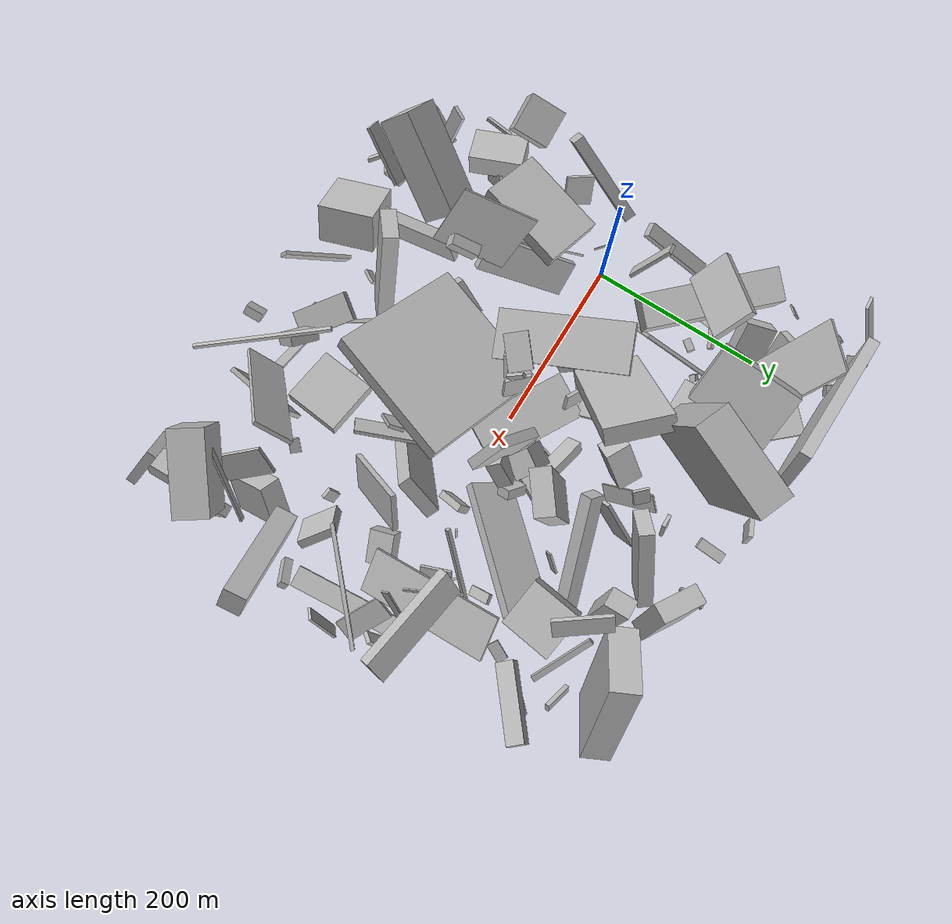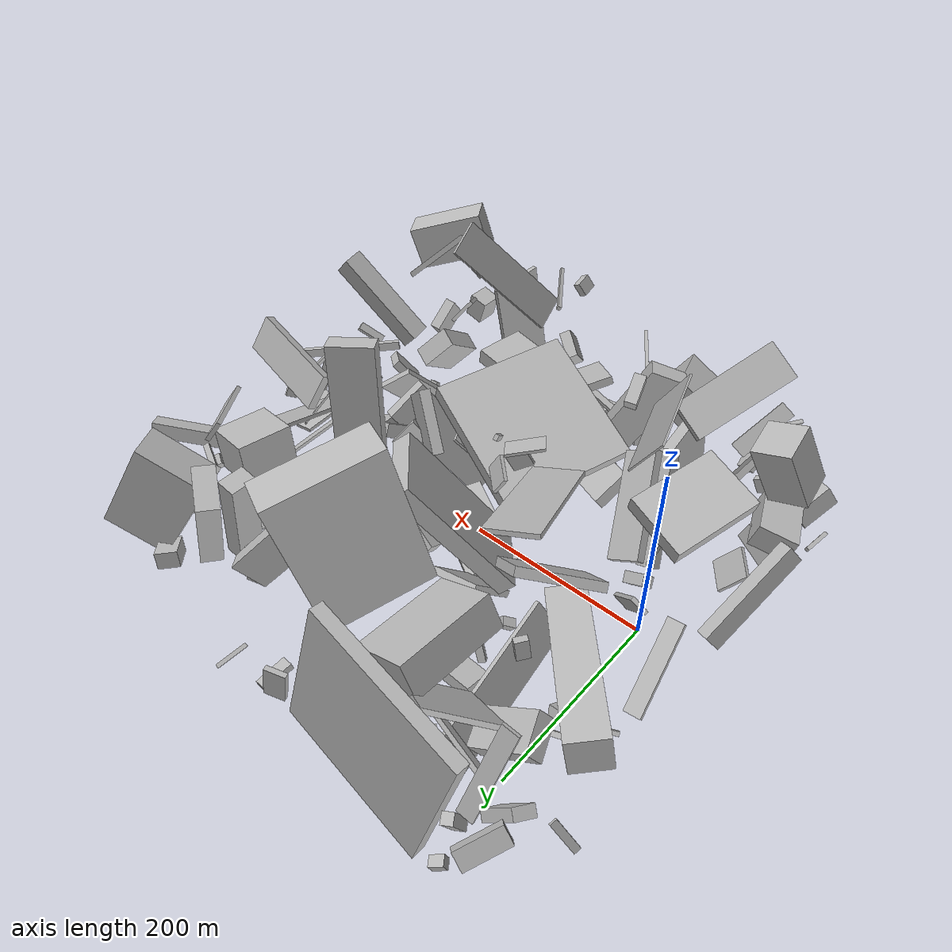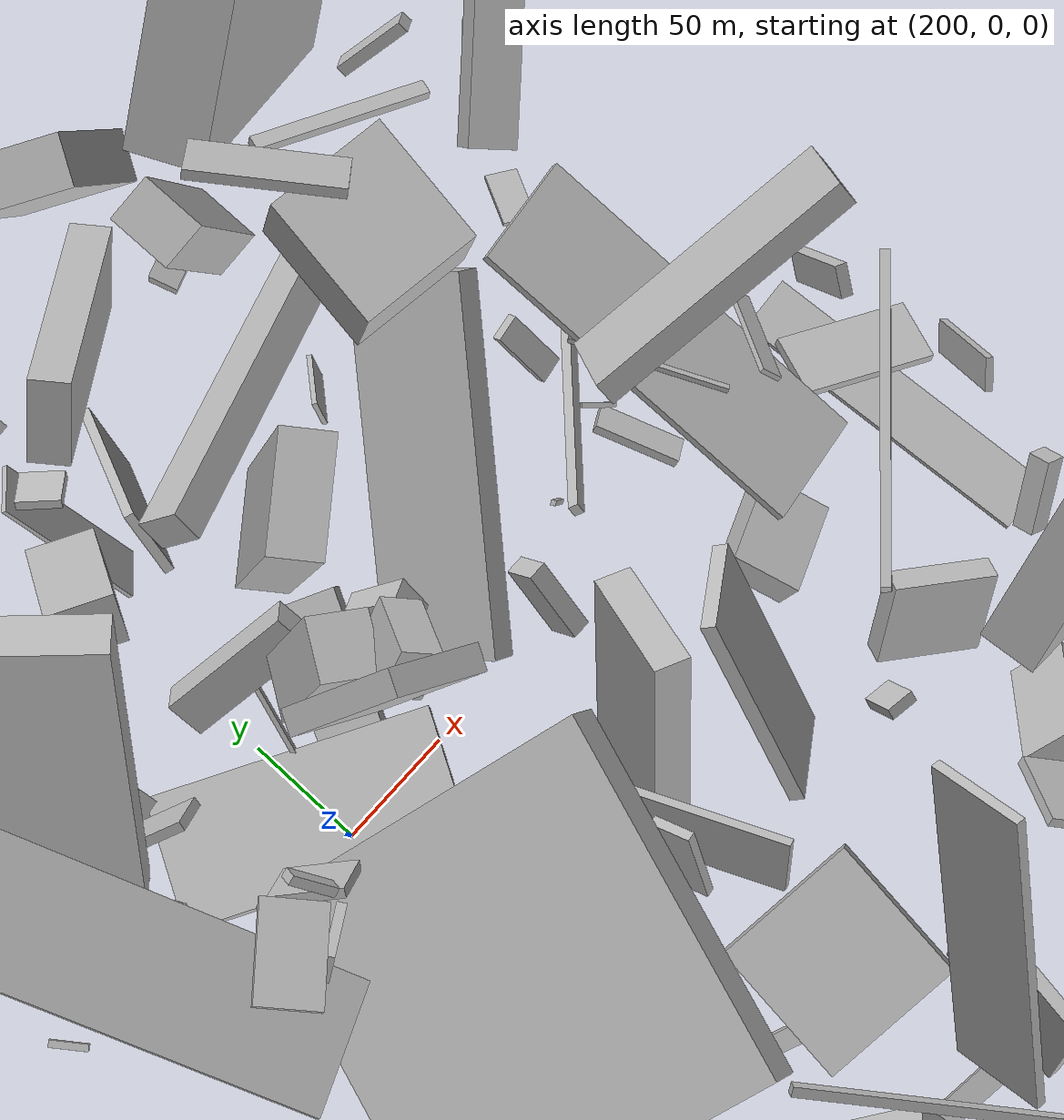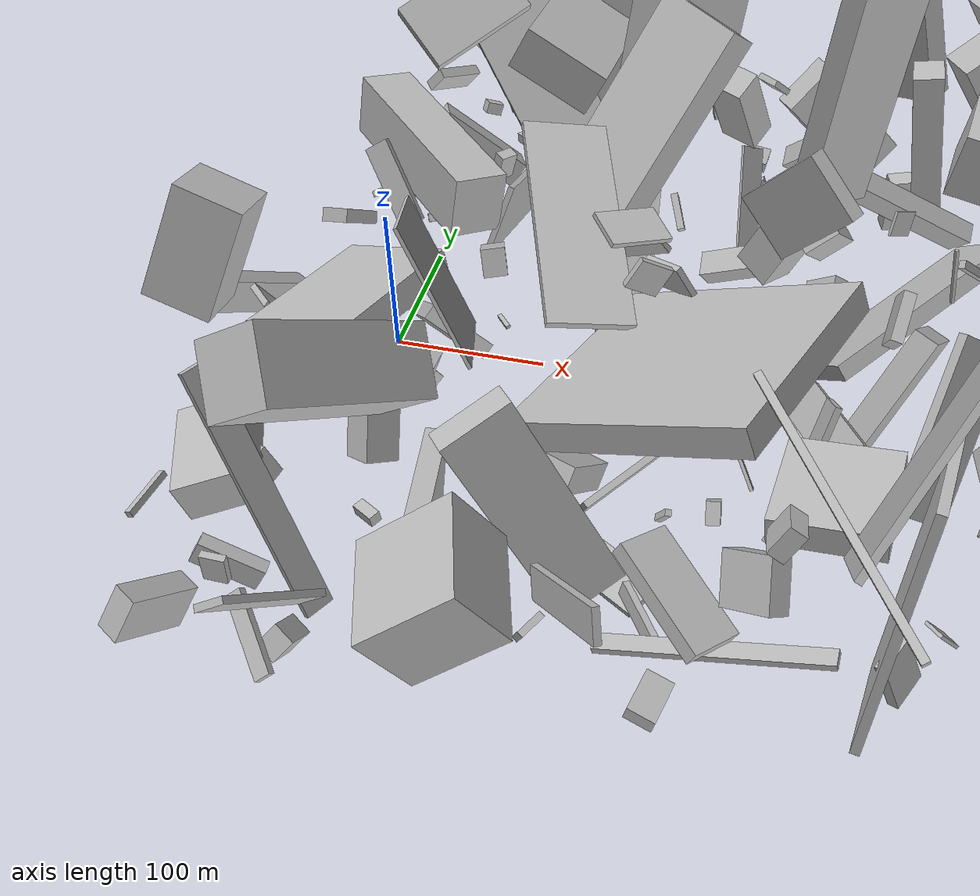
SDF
<sdf version="1.6">
 <world name="default">
  <scene>
   <sky><clouds><speed>12</speed></clouds></sky>
   <ambient>0.4 0.4 0.4 1</ambient>
   <background>0.7 0.7 0.7 1</background>
   <shadows>1</shadows>
  </scene>
  <gravity>0 0 -9.8066</gravity>
  <magnetic_field>6e-06 2.3e-05 -4.2e-05</magnetic_field>
  <physics default="0" name="default_physics" type="ode">
   <ode>
    <solver>
     <type>quick</type>
     <iters>10</iters>
     <sor>1.0</sor>
     <use_dynamic_moi_rescaling>0</use_dynamic_moi_rescaling>
    </solver>
    <constraints>
     <cfm>0</cfm>
     <erp>0.2</erp>
     <contact_max_correcting_vel>100</contact_max_correcting_vel>
     <contact_surface_layer>0.001</contact_surface_layer>
    </constraints>
   </ode>
   <max_step_size>0.004</max_step_size>
   <real_time_factor>1</real_time_factor>
   <real_time_update_rate>250</real_time_update_rate>
  </physics>
  <light name="sun" type="directional">
   <pose>0 0 10 0 0 0</pose>
   <diffuse>0.8 0.8 0.8 1</diffuse>
   <specular>0.2 0.2 0.2 1</specular>
   <attenuation>
    <range>1000</range>
    <constant>0.9</constant>
    <linear>0.01</linear>
    <quadratic>0.001</quadratic>
   </attenuation>
   <direction>-0.5 0.1 -0.9</direction>
  </light>
  <model name="building_1">
   <static>0</static>
   <pose>427.8746247779972 -118.3131937884148 44.31102505832479 1.1717836898685954 -0.6625904021183507 -1.9890397304137952</pose>
   <link name="link">
    <gravity>0</gravity>
    <pose>0 0 21.0 0 0 0</pose>
    <collision name="collision"><geometry><box><size>10 38 42</size></box></geometry></collision>
    <visual name="visual">
     <cast_shadows>0</cast_shadows>
     <geometry><box><size>10 38 42</size></box></geometry>
     <material>
      <script>
       <uri>model://HANNAS_wall/materials/scripts</uri>
       <uri>model://HANNAS_wall/materials/textures</uri>
       <name>vrc/HANNAS_wall</name>
      </script>
     </material>
    </visual>
   </link>
  </model>
  <model name="building_2">
   <static>0</static>
   <pose>440.4431010507671 38.60146053328462 60.069480428920286 -1.1927769694881696 -0.2578235203287633 1.6142492067294447</pose>
   <link name="link">
    <gravity>0</gravity>
    <pose>0 0 24.5 0 0 0</pose>
    <collision name="collision"><geometry><box><size>150 4 49</size></box></geometry></collision>
    <visual name="visual">
     <cast_shadows>0</cast_shadows>
     <geometry><box><size>150 4 49</size></box></geometry>
     <material>
      <script>
       <uri>model://HANNAS_wall/materials/scripts</uri>
       <uri>model://HANNAS_wall/materials/textures</uri>
       <name>vrc/HANNAS_wall</name>
      </script>
     </material>
    </visual>
   </link>
  </model>
  <model name="building_3">
   <static>0</static>
   <pose>130.32142058411907 -123.86306985919583 28.53512889043172 -0.6266059021932514 0.028651438873548412 -0.38265802205027355</pose>
   <link name="link">
    <gravity>0</gravity>
    <pose>0 0 8.5 0 0 0</pose>
    <collision name="collision"><geometry><box><size>52 43 17</size></box></geometry></collision>
    <visual name="visual">
     <cast_shadows>0</cast_shadows>
     <geometry><box><size>52 43 17</size></box></geometry>
     <material>
      <script>
       <uri>model://HANNAS_wall/materials/scripts</uri>
       <uri>model://HANNAS_wall/materials/textures</uri>
       <name>vrc/HANNAS_wall</name>
      </script>
     </material>
    </visual>
   </link>
  </model>
  <model name="building_4">
   <static>0</static>
   <pose>333.0403821662819 -28.217472656530642 92.00969737232062 2.844556248384213 -0.5754585800654934 -1.8473623152837724</pose>
   <link name="link">
    <gravity>0</gravity>
    <pose>0 0 75.0 0 0 0</pose>
    <collision name="collision"><geometry><box><size>49 15 150</size></box></geometry></collision>
    <visual name="visual">
     <cast_shadows>0</cast_shadows>
     <geometry><box><size>49 15 150</size></box></geometry>
     <material>
      <script>
       <uri>model://HANNAS_wall/materials/scripts</uri>
       <uri>model://HANNAS_wall/materials/textures</uri>
       <name>vrc/HANNAS_wall</name>
      </script>
     </material>
    </visual>
   </link>
  </model>
  <model name="building_5">
   <static>0</static>
   <pose>-38.22261522199689 219.21160961585014 27.88847049735415 2.7129642975452604 0.5179901061412655 2.4631052561485425</pose>
   <link name="link">
    <gravity>0</gravity>
    <pose>0 0 24.5 0 0 0</pose>
    <collision name="collision"><geometry><box><size>11 22 49</size></box></geometry></collision>
    <visual name="visual">
     <cast_shadows>0</cast_shadows>
     <geometry><box><size>11 22 49</size></box></geometry>
     <material>
      <script>
       <uri>model://HANNAS_wall/materials/scripts</uri>
       <uri>model://HANNAS_wall/materials/textures</uri>
       <name>vrc/HANNAS_wall</name>
      </script>
     </material>
    </visual>
   </link>
  </model>
  <model name="building_6">
   <static>0</static>
   <pose>388.2095057453608 76.4043435438441 40.05132889341294 1.4428762924801 -0.7577369081922626 -1.315213940994746</pose>
   <link name="link">
    <gravity>0</gravity>
    <pose>0 0 5.5 0 0 0</pose>
    <collision name="collision"><geometry><box><size>4 31 11</size></box></geometry></collision>
    <visual name="visual">
     <cast_shadows>0</cast_shadows>
     <geometry><box><size>4 31 11</size></box></geometry>
     <material>
      <script>
       <uri>model://HANNAS_wall/materials/scripts</uri>
       <uri>model://HANNAS_wall/materials/textures</uri>
       <name>vrc/HANNAS_wall</name>
      </script>
     </material>
    </visual>
   </link>
  </model>
  <model name="building_7">
   <static>0</static>
   <pose>74.64967712619293 -153.0215495308501 40.21853076425288 1.5793829296600626 0.10665073350857512 0.13532440519797143</pose>
   <link name="link">
    <gravity>0</gravity>
    <pose>0 0 49.5 0 0 0</pose>
    <collision name="collision"><geometry><box><size>12 77 99</size></box></geometry></collision>
    <visual name="visual">
     <cast_shadows>0</cast_shadows>
     <geometry><box><size>12 77 99</size></box></geometry>
     <material>
      <script>
       <uri>model://HANNAS_wall/materials/scripts</uri>
       <uri>model://HANNAS_wall/materials/textures</uri>
       <name>vrc/HANNAS_wall</name>
      </script>
     </material>
    </visual>
   </link>
  </model>
  <model name="building_8">
   <static>0</static>
   <pose>-24.237188928174724 -75.06176642458443 92.41174616636208 -1.2998355390156124 -0.11036003465811149 -1.8368349572877083</pose>
   <link name="link">
    <gravity>0</gravity>
    <pose>0 0 34.0 0 0 0</pose>
    <collision name="collision"><geometry><box><size>100 17 68</size></box></geometry></collision>
    <visual name="visual">
     <cast_shadows>0</cast_shadows>
     <geometry><box><size>100 17 68</size></box></geometry>
     <material>
      <script>
       <uri>model://HANNAS_wall/materials/scripts</uri>
       <uri>model://HANNAS_wall/materials/textures</uri>
       <name>vrc/HANNAS_wall</name>
      </script>
     </material>
    </visual>
   </link>
  </model>
  <model name="building_9">
   <static>0</static>
   <pose>39.64252163105623 -27.66770000742519 46.26744664555902 0.7620774624724469 -0.6446618549929659 1.0246427299296357</pose>
   <link name="link">
    <gravity>0</gravity>
    <pose>0 0 55.0 0 0 0</pose>
    <collision name="collision"><geometry><box><size>9 39 110</size></box></geometry></collision>
    <visual name="visual">
     <cast_shadows>0</cast_shadows>
     <geometry><box><size>9 39 110</size></box></geometry>
     <material>
      <script>
       <uri>model://HANNAS_wall/materials/scripts</uri>
       <uri>model://HANNAS_wall/materials/textures</uri>
       <name>vrc/HANNAS_wall</name>
      </script>
     </material>
    </visual>
   </link>
  </model>
  <model name="building_10">
   <static>0</static>
   <pose>232.27764748264298 53.23633769311051 96.22144961448575 2.7284813280096243 -1.1466738281262676 -0.2003672247697847</pose>
   <link name="link">
    <gravity>0</gravity>
    <pose>0 0 12.5 0 0 0</pose>
    <collision name="collision"><geometry><box><size>50 26 25</size></box></geometry></collision>
    <visual name="visual">
     <cast_shadows>0</cast_shadows>
     <geometry><box><size>50 26 25</size></box></geometry>
     <material>
      <script>
       <uri>model://HANNAS_wall/materials/scripts</uri>
       <uri>model://HANNAS_wall/materials/textures</uri>
       <name>vrc/HANNAS_wall</name>
      </script>
     </material>
    </visual>
   </link>
  </model>
  <model name="building_11">
   <static>0</static>
   <pose>149.7832015778629 186.83316816147635 112.1341788793621 0.20476677884110345 -0.03882666111469006 2.753556784348288</pose>
   <link name="link">
    <gravity>0</gravity>
    <pose>0 0 75.0 0 0 0</pose>
    <collision name="collision"><geometry><box><size>36 99 150</size></box></geometry></collision>
    <visual name="visual">
     <cast_shadows>0</cast_shadows>
     <geometry><box><size>36 99 150</size></box></geometry>
     <material>
      <script>
       <uri>model://HANNAS_wall/materials/scripts</uri>
       <uri>model://HANNAS_wall/materials/textures</uri>
       <name>vrc/HANNAS_wall</name>
      </script>
     </material>
    </visual>
   </link>
  </model>
  <model name="building_12">
   <static>0</static>
   <pose>157.24982616215678 -145.59640159223133 27.705705379388718 1.141422459198106 0.9817532152699329 2.0649143481300807</pose>
   <link name="link">
    <gravity>0</gravity>
    <pose>0 0 37.5 0 0 0</pose>
    <collision name="collision"><geometry><box><size>24 4 75</size></box></geometry></collision>
    <visual name="visual">
     <cast_shadows>0</cast_shadows>
     <geometry><box><size>24 4 75</size></box></geometry>
     <material>
      <script>
       <uri>model://HANNAS_wall/materials/scripts</uri>
       <uri>model://HANNAS_wall/materials/textures</uri>
       <name>vrc/HANNAS_wall</name>
      </script>
     </material>
    </visual>
   </link>
  </model>
  <model name="building_13">
   <static>0</static>
   <pose>13.079674641317931 203.46861613408774 96.99087218556744 1.1341920454446301 -0.8229672286603201 2.5607372426709487</pose>
   <link name="link">
    <gravity>0</gravity>
    <pose>0 0 30.5 0 0 0</pose>
    <collision name="collision"><geometry><box><size>150 4 61</size></box></geometry></collision>
    <visual name="visual">
     <cast_shadows>0</cast_shadows>
     <geometry><box><size>150 4 61</size></box></geometry>
     <material>
      <script>
       <uri>model://HANNAS_wall/materials/scripts</uri>
       <uri>model://HANNAS_wall/materials/textures</uri>
       <name>vrc/HANNAS_wall</name>
      </script>
     </material>
    </visual>
   </link>
  </model>
  <model name="building_14">
   <static>0</static>
   <pose>84.24832538760737 158.7853391756359 20.51292014486201 -0.1887595407443927 0.04330623179839676 3.132887912742751</pose>
   <link name="link">
    <gravity>0</gravity>
    <pose>0 0 6.0 0 0 0</pose>
    <collision name="collision"><geometry><box><size>39 27 12</size></box></geometry></collision>
    <visual name="visual">
     <cast_shadows>0</cast_shadows>
     <geometry><box><size>39 27 12</size></box></geometry>
     <material>
      <script>
       <uri>model://HANNAS_wall/materials/scripts</uri>
       <uri>model://HANNAS_wall/materials/textures</uri>
       <name>vrc/HANNAS_wall</name>
      </script>
     </material>
    </visual>
   </link>
  </model>
  <model name="building_15">
   <static>0</static>
   <pose>219.52609646362248 64.4884611498182 48.07759273776928 -0.7598916400136252 0.8958230802810724 0.7362716197174718</pose>
   <link name="link">
    <gravity>0</gravity>
    <pose>0 0 8.5 0 0 0</pose>
    <collision name="collision"><geometry><box><size>13 59 17</size></box></geometry></collision>
    <visual name="visual">
     <cast_shadows>0</cast_shadows>
     <geometry><box><size>13 59 17</size></box></geometry>
     <material>
      <script>
       <uri>model://HANNAS_wall/materials/scripts</uri>
       <uri>model://HANNAS_wall/materials/textures</uri>
       <name>vrc/HANNAS_wall</name>
      </script>
     </material>
    </visual>
   </link>
  </model>
  <model name="building_16">
   <static>0</static>
   <pose>404.9165418594119 -195.5237924178775 52.461560579459025 2.518352501273381 -0.6049603325659582 1.6710902150607259</pose>
   <link name="link">
    <gravity>0</gravity>
    <pose>0 0 23.0 0 0 0</pose>
    <collision name="collision"><geometry><box><size>60 24 46</size></box></geometry></collision>
    <visual name="visual">
     <cast_shadows>0</cast_shadows>
     <geometry><box><size>60 24 46</size></box></geometry>
     <material>
      <script>
       <uri>model://HANNAS_wall/materials/scripts</uri>
       <uri>model://HANNAS_wall/materials/textures</uri>
       <name>vrc/HANNAS_wall</name>
      </script>
     </material>
    </visual>
   </link>
  </model>
  <model name="building_17">
   <static>0</static>
   <pose>335.90783788194483 195.53766606975177 89.73078323857001 1.7374953841887708 -0.007283260920793814 -1.5533922045461594</pose>
   <link name="link">
    <gravity>0</gravity>
    <pose>0 0 10.0 0 0 0</pose>
    <collision name="collision"><geometry><box><size>27 102 20</size></box></geometry></collision>
    <visual name="visual">
     <cast_shadows>0</cast_shadows>
     <geometry><box><size>27 102 20</size></box></geometry>
     <material>
      <script>
       <uri>model://HANNAS_wall/materials/scripts</uri>
       <uri>model://HANNAS_wall/materials/textures</uri>
       <name>vrc/HANNAS_wall</name>
      </script>
     </material>
    </visual>
   </link>
  </model>
  <model name="building_18">
   <static>0</static>
   <pose>8.267739252990763 -209.35803108081714 76.60720962808759 -1.6518469985844302 -1.1276937638027322 2.6891633907499535</pose>
   <link name="link">
    <gravity>0</gravity>
    <pose>0 0 8.5 0 0 0</pose>
    <collision name="collision"><geometry><box><size>150 4 17</size></box></geometry></collision>
    <visual name="visual">
     <cast_shadows>0</cast_shadows>
     <geometry><box><size>150 4 17</size></box></geometry>
     <material>
      <script>
       <uri>model://HANNAS_wall/materials/scripts</uri>
       <uri>model://HANNAS_wall/materials/textures</uri>
       <name>vrc/HANNAS_wall</name>
      </script>
     </material>
    </visual>
   </link>
  </model>
  <model name="building_19">
   <static>0</static>
   <pose>281.5078943689698 -105.79676110662123 68.86743471104913 2.0296644123883323 -0.33999283747577513 -2.98777704350968</pose>
   <link name="link">
    <gravity>0</gravity>
    <pose>0 0 8.5 0 0 0</pose>
    <collision name="collision"><geometry><box><size>4 42 17</size></box></geometry></collision>
    <visual name="visual">
     <cast_shadows>0</cast_shadows>
     <geometry><box><size>4 42 17</size></box></geometry>
     <material>
      <script>
       <uri>model://HANNAS_wall/materials/scripts</uri>
       <uri>model://HANNAS_wall/materials/textures</uri>
       <name>vrc/HANNAS_wall</name>
      </script>
     </material>
    </visual>
   </link>
  </model>
  <model name="building_20">
   <static>0</static>
   <pose>214.78213762172194 207.93914817287515 21.610456366089423 -2.060364451368353 -1.1821395013426674 -2.626097188958331</pose>
   <link name="link">
    <gravity>0</gravity>
    <pose>0 0 2.0 0 0 0</pose>
    <collision name="collision"><geometry><box><size>23 16 4</size></box></geometry></collision>
    <visual name="visual">
     <cast_shadows>0</cast_shadows>
     <geometry><box><size>23 16 4</size></box></geometry>
     <material>
      <script>
       <uri>model://HANNAS_wall/materials/scripts</uri>
       <uri>model://HANNAS_wall/materials/textures</uri>
       <name>vrc/HANNAS_wall</name>
      </script>
     </material>
    </visual>
   </link>
  </model>
  <model name="building_21">
   <static>0</static>
   <pose>206.00596392958312 -88.20786246817127 83.86686261471118 -0.072227678789199 -0.42045399274548895 -0.29405858357691567</pose>
   <link name="link">
    <gravity>0</gravity>
    <pose>0 0 9.0 0 0 0</pose>
    <collision name="collision"><geometry><box><size>150 150 18</size></box></geometry></collision>
    <visual name="visual">
     <cast_shadows>0</cast_shadows>
     <geometry><box><size>150 150 18</size></box></geometry>
     <material>
      <script>
       <uri>model://HANNAS_wall/materials/scripts</uri>
       <uri>model://HANNAS_wall/materials/textures</uri>
       <name>vrc/HANNAS_wall</name>
      </script>
     </material>
    </visual>
   </link>
  </model>
  <model name="building_22">
   <static>0</static>
   <pose>457.55900169558515 -232.11853981129252 37.44520186995703 -0.692716554193236 -0.17643118602930716 0.1422758287269079</pose>
   <link name="link">
    <gravity>0</gravity>
    <pose>0 0 17.0 0 0 0</pose>
    <collision name="collision"><geometry><box><size>13 40 34</size></box></geometry></collision>
    <visual name="visual">
     <cast_shadows>0</cast_shadows>
     <geometry><box><size>13 40 34</size></box></geometry>
     <material>
      <script>
       <uri>model://HANNAS_wall/materials/scripts</uri>
       <uri>model://HANNAS_wall/materials/textures</uri>
       <name>vrc/HANNAS_wall</name>
      </script>
     </material>
    </visual>
   </link>
  </model>
  <model name="building_23">
   <static>0</static>
   <pose>338.70299949811437 56.00060980796596 46.621645672576314 2.2432393264583905 0.24130760410190355 -2.3062253183938997</pose>
   <link name="link">
    <gravity>0</gravity>
    <pose>0 0 27.5 0 0 0</pose>
    <collision name="collision"><geometry><box><size>150 11 55</size></box></geometry></collision>
    <visual name="visual">
     <cast_shadows>0</cast_shadows>
     <geometry><box><size>150 11 55</size></box></geometry>
     <material>
      <script>
       <uri>model://HANNAS_wall/materials/scripts</uri>
       <uri>model://HANNAS_wall/materials/textures</uri>
       <name>vrc/HANNAS_wall</name>
      </script>
     </material>
    </visual>
   </link>
  </model>
  <model name="building_24">
   <static>0</static>
   <pose>180.85534049957624 -174.2226100584998 9.97281800642865 -0.22162244341089382 0.04831437497987815 2.5471112307758186</pose>
   <link name="link">
    <gravity>0</gravity>
    <pose>0 0 2.0 0 0 0</pose>
    <collision name="collision"><geometry><box><size>51 25 4</size></box></geometry></collision>
    <visual name="visual">
     <cast_shadows>0</cast_shadows>
     <geometry><box><size>51 25 4</size></box></geometry>
     <material>
      <script>
       <uri>model://HANNAS_wall/materials/scripts</uri>
       <uri>model://HANNAS_wall/materials/textures</uri>
       <name>vrc/HANNAS_wall</name>
      </script>
     </material>
    </visual>
   </link>
  </model>
  <model name="building_25">
   <static>0</static>
   <pose>39.34662734941924 127.38842771322213 58.66783335978796 0.08200566092922057 -0.24210005695025313 2.485799372037489</pose>
   <link name="link">
    <gravity>0</gravity>
    <pose>0 0 9.5 0 0 0</pose>
    <collision name="collision"><geometry><box><size>8 13 19</size></box></geometry></collision>
    <visual name="visual">
     <cast_shadows>0</cast_shadows>
     <geometry><box><size>8 13 19</size></box></geometry>
     <material>
      <script>
       <uri>model://HANNAS_wall/materials/scripts</uri>
       <uri>model://HANNAS_wall/materials/textures</uri>
       <name>vrc/HANNAS_wall</name>
      </script>
     </material>
    </visual>
   </link>
  </model>
  <model name="building_26">
   <static>0</static>
   <pose>282.6862878299945 -237.7688720652819 154.57431084941203 -0.5239118822449449 -1.093765262758287 -2.053086634645284</pose>
   <link name="link">
    <gravity>0</gravity>
    <pose>0 0 2.0 0 0 0</pose>
    <collision name="collision"><geometry><box><size>4 148 4</size></box></geometry></collision>
    <visual name="visual">
     <cast_shadows>0</cast_shadows>
     <geometry><box><size>4 148 4</size></box></geometry>
     <material>
      <script>
       <uri>model://HANNAS_wall/materials/scripts</uri>
       <uri>model://HANNAS_wall/materials/textures</uri>
       <name>vrc/HANNAS_wall</name>
      </script>
     </material>
    </visual>
   </link>
  </model>
  <model name="building_27">
   <static>0</static>
   <pose>393.2907997637555 136.81611679598745 109.39895591986141 1.4267878230865503 0.03693590992971222 -1.7060419672237959</pose>
   <link name="link">
    <gravity>0</gravity>
    <pose>0 0 25.5 0 0 0</pose>
    <collision name="collision"><geometry><box><size>55 44 51</size></box></geometry></collision>
    <visual name="visual">
     <cast_shadows>0</cast_shadows>
     <geometry><box><size>55 44 51</size></box></geometry>
     <material>
      <script>
       <uri>model://HANNAS_wall/materials/scripts</uri>
       <uri>model://HANNAS_wall/materials/textures</uri>
       <name>vrc/HANNAS_wall</name>
      </script>
     </material>
    </visual>
   </link>
  </model>
  <model name="building_28">
   <static>0</static>
   <pose>-24.104970180679537 107.04220451020208 78.22535698041028 1.726099186340496 -0.03131759160626407 2.3228075723336823</pose>
   <link name="link">
    <gravity>0</gravity>
    <pose>0 0 18.5 0 0 0</pose>
    <collision name="collision"><geometry><box><size>150 42 37</size></box></geometry></collision>
    <visual name="visual">
     <cast_shadows>0</cast_shadows>
     <geometry><box><size>150 42 37</size></box></geometry>
     <material>
      <script>
       <uri>model://HANNAS_wall/materials/scripts</uri>
       <uri>model://HANNAS_wall/materials/textures</uri>
       <name>vrc/HANNAS_wall</name>
      </script>
     </material>
    </visual>
   </link>
  </model>
  <model name="building_29">
   <static>0</static>
   <pose>-69.42836918475011 -52.817225859636466 65.09020769886938 -1.2588977951005393 0.6035472775964869 1.3226189601937945</pose>
   <link name="link">
    <gravity>0</gravity>
    <pose>0 0 6.5 0 0 0</pose>
    <collision name="collision"><geometry><box><size>109 22 13</size></box></geometry></collision>
    <visual name="visual">
     <cast_shadows>0</cast_shadows>
     <geometry><box><size>109 22 13</size></box></geometry>
     <material>
      <script>
       <uri>model://HANNAS_wall/materials/scripts</uri>
       <uri>model://HANNAS_wall/materials/textures</uri>
       <name>vrc/HANNAS_wall</name>
      </script>
     </material>
    </visual>
   </link>
  </model>
  <model name="building_30">
   <static>0</static>
   <pose>83.32996170653394 198.32071532135723 141.20286087648145 2.6658873330432473 -0.027324226033345975 -1.6343026786071377</pose>
   <link name="link">
    <gravity>0</gravity>
    <pose>0 0 16.0 0 0 0</pose>
    <collision name="collision"><geometry><box><size>90 62 32</size></box></geometry></collision>
    <visual name="visual">
     <cast_shadows>0</cast_shadows>
     <geometry><box><size>90 62 32</size></box></geometry>
     <material>
      <script>
       <uri>model://HANNAS_wall/materials/scripts</uri>
       <uri>model://HANNAS_wall/materials/textures</uri>
       <name>vrc/HANNAS_wall</name>
      </script>
     </material>
    </visual>
   </link>
  </model>
  <model name="building_31">
   <static>0</static>
   <pose>23.712993987857796 225.48053593789643 73.78644254102036 0.6964478640824776 0.6205880064474074 1.591387743899397</pose>
   <link name="link">
    <gravity>0</gravity>
    <pose>0 0 4.5 0 0 0</pose>
    <collision name="collision"><geometry><box><size>4 150 9</size></box></geometry></collision>
    <visual name="visual">
     <cast_shadows>0</cast_shadows>
     <geometry><box><size>4 150 9</size></box></geometry>
     <material>
      <script>
       <uri>model://HANNAS_wall/materials/scripts</uri>
       <uri>model://HANNAS_wall/materials/textures</uri>
       <name>vrc/HANNAS_wall</name>
      </script>
     </material>
    </visual>
   </link>
  </model>
  <model name="building_32">
   <static>0</static>
   <pose>400.26145545715553 237.65232030737445 28.487578933202496 0.16859323836312462 1.3529740922339082 2.580095224468473</pose>
   <link name="link">
    <gravity>0</gravity>
    <pose>0 0 13.5 0 0 0</pose>
    <collision name="collision"><geometry><box><size>18 22 27</size></box></geometry></collision>
    <visual name="visual">
     <cast_shadows>0</cast_shadows>
     <geometry><box><size>18 22 27</size></box></geometry>
     <material>
      <script>
       <uri>model://HANNAS_wall/materials/scripts</uri>
       <uri>model://HANNAS_wall/materials/textures</uri>
       <name>vrc/HANNAS_wall</name>
      </script>
     </material>
    </visual>
   </link>
  </model>
  <model name="building_33">
   <static>0</static>
   <pose>292.96228329793706 217.71010325587122 53.25038979860694 0.008983599827297436 -0.7369748713210755 0.6411146286087552</pose>
   <link name="link">
    <gravity>0</gravity>
    <pose>0 0 51.0 0 0 0</pose>
    <collision name="collision"><geometry><box><size>37 16 102</size></box></geometry></collision>
    <visual name="visual">
     <cast_shadows>0</cast_shadows>
     <geometry><box><size>37 16 102</size></box></geometry>
     <material>
      <script>
       <uri>model://HANNAS_wall/materials/scripts</uri>
       <uri>model://HANNAS_wall/materials/textures</uri>
       <name>vrc/HANNAS_wall</name>
      </script>
     </material>
    </visual>
   </link>
  </model>
  <model name="building_34">
   <static>0</static>
   <pose>-49.15141833828519 -169.9226055189526 57.79662663016574 2.8681894875074896 -0.057961965504641375 1.9319025093207793</pose>
   <link name="link">
    <gravity>0</gravity>
    <pose>0 0 13.0 0 0 0</pose>
    <collision name="collision"><geometry><box><size>61 41 26</size></box></geometry></collision>
    <visual name="visual">
     <cast_shadows>0</cast_shadows>
     <geometry><box><size>61 41 26</size></box></geometry>
     <material>
      <script>
       <uri>model://HANNAS_wall/materials/scripts</uri>
       <uri>model://HANNAS_wall/materials/textures</uri>
       <name>vrc/HANNAS_wall</name>
      </script>
     </material>
    </visual>
   </link>
  </model>
  <model name="building_35">
   <static>0</static>
   <pose>112.2686175401964 64.9411013371456 72.48270909858081 -0.6241273816576757 0.0033706875729387423 -0.807209717213467</pose>
   <link name="link">
    <gravity>0</gravity>
    <pose>0 0 75.0 0 0 0</pose>
    <collision name="collision"><geometry><box><size>70 18 150</size></box></geometry></collision>
    <visual name="visual">
     <cast_shadows>0</cast_shadows>
     <geometry><box><size>70 18 150</size></box></geometry>
     <material>
      <script>
       <uri>model://HANNAS_wall/materials/scripts</uri>
       <uri>model://HANNAS_wall/materials/textures</uri>
       <name>vrc/HANNAS_wall</name>
      </script>
     </material>
    </visual>
   </link>
  </model>
  <model name="building_36">
   <static>0</static>
   <pose>331.78096026861755 -231.14146185622425 46.38496047689107 2.4980919687394896 -1.1951999043028168 -3.0077103294234524</pose>
   <link name="link">
    <gravity>0</gravity>
    <pose>0 0 3.0 0 0 0</pose>
    <collision name="collision"><geometry><box><size>30 21 6</size></box></geometry></collision>
    <visual name="visual">
     <cast_shadows>0</cast_shadows>
     <geometry><box><size>30 21 6</size></box></geometry>
     <material>
      <script>
       <uri>model://HANNAS_wall/materials/scripts</uri>
       <uri>model://HANNAS_wall/materials/textures</uri>
       <name>vrc/HANNAS_wall</name>
      </script>
     </material>
    </visual>
   </link>
  </model>
  <model name="building_37">
   <static>0</static>
   <pose>33.78213592871217 -109.16914585912318 35.30192318245844 -1.172118982560382 0.42329367469018214 2.5098380651380197</pose>
   <link name="link">
    <gravity>0</gravity>
    <pose>0 0 10.5 0 0 0</pose>
    <collision name="collision"><geometry><box><size>24 44 21</size></box></geometry></collision>
    <visual name="visual">
     <cast_shadows>0</cast_shadows>
     <geometry><box><size>24 44 21</size></box></geometry>
     <material>
      <script>
       <uri>model://HANNAS_wall/materials/scripts</uri>
       <uri>model://HANNAS_wall/materials/textures</uri>
       <name>vrc/HANNAS_wall</name>
      </script>
     </material>
    </visual>
   </link>
  </model>
  <model name="building_38">
   <static>0</static>
   <pose>136.95603371561702 -187.96565766269796 74.18942441103826 -1.1073607272282395 -1.1274468159053326 -2.9382239267700743</pose>
   <link name="link">
    <gravity>0</gravity>
    <pose>0 0 8.5 0 0 0</pose>
    <collision name="collision"><geometry><box><size>136 41 17</size></box></geometry></collision>
    <visual name="visual">
     <cast_shadows>0</cast_shadows>
     <geometry><box><size>136 41 17</size></box></geometry>
     <material>
      <script>
       <uri>model://HANNAS_wall/materials/scripts</uri>
       <uri>model://HANNAS_wall/materials/textures</uri>
       <name>vrc/HANNAS_wall</name>
      </script>
     </material>
    </visual>
   </link>
  </model>
  <model name="building_39">
   <static>0</static>
   <pose>181.55552338361963 -3.8029846837589183 134.0268884696801 -0.7129458847645467 0.28172223112817185 -2.919422960539921</pose>
   <link name="link">
    <gravity>0</gravity>
    <pose>0 0 3.0 0 0 0</pose>
    <collision name="collision"><geometry><box><size>4 21 6</size></box></geometry></collision>
    <visual name="visual">
     <cast_shadows>0</cast_shadows>
     <geometry><box><size>4 21 6</size></box></geometry>
     <material>
      <script>
       <uri>model://HANNAS_wall/materials/scripts</uri>
       <uri>model://HANNAS_wall/materials/textures</uri>
       <name>vrc/HANNAS_wall</name>
      </script>
     </material>
    </visual>
   </link>
  </model>
  <model name="building_40">
   <static>0</static>
   <pose>398.82538052793393 -43.70706958780932 18.89376000352018 -2.8543160169609494 0.35547012998366434 0.3767872537508349</pose>
   <link name="link">
    <gravity>0</gravity>
    <pose>0 0 8.5 0 0 0</pose>
    <collision name="collision"><geometry><box><size>38 29 17</size></box></geometry></collision>
    <visual name="visual">
     <cast_shadows>0</cast_shadows>
     <geometry><box><size>38 29 17</size></box></geometry>
     <material>
      <script>
       <uri>model://HANNAS_wall/materials/scripts</uri>
       <uri>model://HANNAS_wall/materials/textures</uri>
       <name>vrc/HANNAS_wall</name>
      </script>
     </material>
    </visual>
   </link>
  </model>
  <model name="building_41">
   <static>0</static>
   <pose>0.546215693451849 199.4236333749245 40.03255643686731 1.111179175049241 -0.8403933101512087 0.7214751072270812</pose>
   <link name="link">
    <gravity>0</gravity>
    <pose>0 0 18.0 0 0 0</pose>
    <collision name="collision"><geometry><box><size>19 69 36</size></box></geometry></collision>
    <visual name="visual">
     <cast_shadows>0</cast_shadows>
     <geometry><box><size>19 69 36</size></box></geometry>
     <material>
      <script>
       <uri>model://HANNAS_wall/materials/scripts</uri>
       <uri>model://HANNAS_wall/materials/textures</uri>
       <name>vrc/HANNAS_wall</name>
      </script>
     </material>
    </visual>
   </link>
  </model>
  <model name="building_42">
   <static>0</static>
   <pose>230.42341458796216 130.35768904068766 43.8923229715444 -2.2987278374421627 -0.07417734554825312 -0.30571200952292893</pose>
   <link name="link">
    <gravity>0</gravity>
    <pose>0 0 33.5 0 0 0</pose>
    <collision name="collision"><geometry><box><size>4 35 67</size></box></geometry></collision>
    <visual name="visual">
     <cast_shadows>0</cast_shadows>
     <geometry><box><size>4 35 67</size></box></geometry>
     <material>
      <script>
       <uri>model://HANNAS_wall/materials/scripts</uri>
       <uri>model://HANNAS_wall/materials/textures</uri>
       <name>vrc/HANNAS_wall</name>
      </script>
     </material>
    </visual>
   </link>
  </model>
  <model name="building_43">
   <static>0</static>
   <pose>456.5854649477096 -283.6110693227392 48.56442587525281 -3.1227469139394164 1.2705868520333456 0.050129803074393534</pose>
   <link name="link">
    <gravity>0</gravity>
    <pose>0 0 12.0 0 0 0</pose>
    <collision name="collision"><geometry><box><size>31 29 24</size></box></geometry></collision>
    <visual name="visual">
     <cast_shadows>0</cast_shadows>
     <geometry><box><size>31 29 24</size></box></geometry>
     <material>
      <script>
       <uri>model://HANNAS_wall/materials/scripts</uri>
       <uri>model://HANNAS_wall/materials/textures</uri>
       <name>vrc/HANNAS_wall</name>
      </script>
     </material>
    </visual>
   </link>
  </model>
  <model name="building_44">
   <static>0</static>
   <pose>416.575308794752 -222.19508551864763 82.32995958760702 0.9332422184919622 -0.7020246982641462 -2.056849052278858</pose>
   <link name="link">
    <gravity>0</gravity>
    <pose>0 0 32.5 0 0 0</pose>
    <collision name="collision"><geometry><box><size>32 4 65</size></box></geometry></collision>
    <visual name="visual">
     <cast_shadows>0</cast_shadows>
     <geometry><box><size>32 4 65</size></box></geometry>
     <material>
      <script>
       <uri>model://HANNAS_wall/materials/scripts</uri>
       <uri>model://HANNAS_wall/materials/textures</uri>
       <name>vrc/HANNAS_wall</name>
      </script>
     </material>
    </visual>
   </link>
  </model>
  <model name="building_45">
   <static>0</static>
   <pose>329.3016889136294 -190.97209809536005 82.43286395374668 1.4242539517256108 0.04899805646189071 -0.15519452106775286</pose>
   <link name="link">
    <gravity>0</gravity>
    <pose>0 0 30.5 0 0 0</pose>
    <collision name="collision"><geometry><box><size>5 150 61</size></box></geometry></collision>
    <visual name="visual">
     <cast_shadows>0</cast_shadows>
     <geometry><box><size>5 150 61</size></box></geometry>
     <material>
      <script>
       <uri>model://HANNAS_wall/materials/scripts</uri>
       <uri>model://HANNAS_wall/materials/textures</uri>
       <name>vrc/HANNAS_wall</name>
      </script>
     </material>
    </visual>
   </link>
  </model>
  <model name="building_46">
   <static>0</static>
   <pose>104.73765831177516 -118.73236171235021 161.3383829701817 0.09613063901894432 -0.5293689854864211 -1.290899023836904</pose>
   <link name="link">
    <gravity>0</gravity>
    <pose>0 0 7.0 0 0 0</pose>
    <collision name="collision"><geometry><box><size>31 12 14</size></box></geometry></collision>
    <visual name="visual">
     <cast_shadows>0</cast_shadows>
     <geometry><box><size>31 12 14</size></box></geometry>
     <material>
      <script>
       <uri>model://HANNAS_wall/materials/scripts</uri>
       <uri>model://HANNAS_wall/materials/textures</uri>
       <name>vrc/HANNAS_wall</name>
      </script>
     </material>
    </visual>
   </link>
  </model>
  <model name="building_47">
   <static>0</static>
   <pose>-62.49550309913893 -134.81367436308233 129.8701430130713 0.2920165682109214 -0.3462352591781784 3.1368918423460634</pose>
   <link name="link">
    <gravity>0</gravity>
    <pose>0 0 32.5 0 0 0</pose>
    <collision name="collision"><geometry><box><size>38 38 65</size></box></geometry></collision>
    <visual name="visual">
     <cast_shadows>0</cast_shadows>
     <geometry><box><size>38 38 65</size></box></geometry>
     <material>
      <script>
       <uri>model://HANNAS_wall/materials/scripts</uri>
       <uri>model://HANNAS_wall/materials/textures</uri>
       <name>vrc/HANNAS_wall</name>
      </script>
     </material>
    </visual>
   </link>
  </model>
  <model name="building_48">
   <static>0</static>
   <pose>60.78758345793965 272.80892171845113 105.03418474843198 1.4515096609376705 0.23076253464599644 3.0775765544457685</pose>
   <link name="link">
    <gravity>0</gravity>
    <pose>0 0 6.0 0 0 0</pose>
    <collision name="collision"><geometry><box><size>150 150 12</size></box></geometry></collision>
    <visual name="visual">
     <cast_shadows>0</cast_shadows>
     <geometry><box><size>150 150 12</size></box></geometry>
     <material>
      <script>
       <uri>model://HANNAS_wall/materials/scripts</uri>
       <uri>model://HANNAS_wall/materials/textures</uri>
       <name>vrc/HANNAS_wall</name>
      </script>
     </material>
    </visual>
   </link>
  </model>
  <model name="building_49">
   <static>0</static>
   <pose>17.715322219001706 -39.04278381000216 23.00061728601557 -2.2847181453704177 0.5911410377605386 -2.190799577122648</pose>
   <link name="link">
    <gravity>0</gravity>
    <pose>0 0 14.0 0 0 0</pose>
    <collision name="collision"><geometry><box><size>13 12 28</size></box></geometry></collision>
    <visual name="visual">
     <cast_shadows>0</cast_shadows>
     <geometry><box><size>13 12 28</size></box></geometry>
     <material>
      <script>
       <uri>model://HANNAS_wall/materials/scripts</uri>
       <uri>model://HANNAS_wall/materials/textures</uri>
       <name>vrc/HANNAS_wall</name>
      </script>
     </material>
    </visual>
   </link>
  </model>
  <model name="building_50">
   <static>0</static>
   <pose>147.36741980478376 59.81347581720005 55.495108072719574 0.3999021118568432 -0.48585957737385504 -0.4306829690289839</pose>
   <link name="link">
    <gravity>0</gravity>
    <pose>0 0 9.0 0 0 0</pose>
    <collision name="collision"><geometry><box><size>62 4 18</size></box></geometry></collision>
    <visual name="visual">
     <cast_shadows>0</cast_shadows>
     <geometry><box><size>62 4 18</size></box></geometry>
     <material>
      <script>
       <uri>model://HANNAS_wall/materials/scripts</uri>
       <uri>model://HANNAS_wall/materials/textures</uri>
       <name>vrc/HANNAS_wall</name>
      </script>
     </material>
    </visual>
   </link>
  </model>
  <model name="building_51">
   <static>0</static>
   <pose>32.5086295257191 -259.7795285765354 27.77272644836856 -2.4842297090578582 0.6727064203651336 1.5876106021687812</pose>
   <link name="link">
    <gravity>0</gravity>
    <pose>0 0 7.5 0 0 0</pose>
    <collision name="collision"><geometry><box><size>24 13 15</size></box></geometry></collision>
    <visual name="visual">
     <cast_shadows>0</cast_shadows>
     <geometry><box><size>24 13 15</size></box></geometry>
     <material>
      <script>
       <uri>model://HANNAS_wall/materials/scripts</uri>
       <uri>model://HANNAS_wall/materials/textures</uri>
       <name>vrc/HANNAS_wall</name>
      </script>
     </material>
    </visual>
   </link>
  </model>
  <model name="building_52">
   <static>0</static>
   <pose>244.76180193425367 -220.6103196842091 81.41164423824289 0.7081499343680119 -0.8199032074183296 1.7153699720471818</pose>
   <link name="link">
    <gravity>0</gravity>
    <pose>0 0 16.0 0 0 0</pose>
    <collision name="collision"><geometry><box><size>28 13 32</size></box></geometry></collision>
    <visual name="visual">
     <cast_shadows>0</cast_shadows>
     <geometry><box><size>28 13 32</size></box></geometry>
     <material>
      <script>
       <uri>model://HANNAS_wall/materials/scripts</uri>
       <uri>model://HANNAS_wall/materials/textures</uri>
       <name>vrc/HANNAS_wall</name>
      </script>
     </material>
    </visual>
   </link>
  </model>
  <model name="building_53">
   <static>0</static>
   <pose>119.15319104596935 12.087437967617419 109.7444140205364 2.804063841022327 -0.17099700770774534 -2.741890085100967</pose>
   <link name="link">
    <gravity>0</gravity>
    <pose>0 0 2.5 0 0 0</pose>
    <collision name="collision"><geometry><box><size>54 150 5</size></box></geometry></collision>
    <visual name="visual">
     <cast_shadows>0</cast_shadows>
     <geometry><box><size>54 150 5</size></box></geometry>
     <material>
      <script>
       <uri>model://HANNAS_wall/materials/scripts</uri>
       <uri>model://HANNAS_wall/materials/textures</uri>
       <name>vrc/HANNAS_wall</name>
      </script>
     </material>
    </visual>
   </link>
  </model>
  <model name="building_54">
   <static>0</static>
   <pose>269.64176747127465 -257.2484152795081 154.2158566773842 1.03614849763451 -0.2653974276717952 -1.5009753607057454</pose>
   <link name="link">
    <gravity>0</gravity>
    <pose>0 0 4.5 0 0 0</pose>
    <collision name="collision"><geometry><box><size>18 16 9</size></box></geometry></collision>
    <visual name="visual">
     <cast_shadows>0</cast_shadows>
     <geometry><box><size>18 16 9</size></box></geometry>
     <material>
      <script>
       <uri>model://HANNAS_wall/materials/scripts</uri>
       <uri>model://HANNAS_wall/materials/textures</uri>
       <name>vrc/HANNAS_wall</name>
      </script>
     </material>
    </visual>
   </link>
  </model>
  <model name="building_55">
   <static>0</static>
   <pose>447.6871426932669 -45.520979965476585 90.10458429010048 -0.1017557220480183 0.09683040172243444 0.7320234597085364</pose>
   <link name="link">
    <gravity>0</gravity>
    <pose>0 0 5.5 0 0 0</pose>
    <collision name="collision"><geometry><box><size>127 4 11</size></box></geometry></collision>
    <visual name="visual">
     <cast_shadows>0</cast_shadows>
     <geometry><box><size>127 4 11</size></box></geometry>
     <material>
      <script>
       <uri>model://HANNAS_wall/materials/scripts</uri>
       <uri>model://HANNAS_wall/materials/textures</uri>
       <name>vrc/HANNAS_wall</name>
      </script>
     </material>
    </visual>
   </link>
  </model>
  <model name="building_56">
   <static>0</static>
   <pose>454.8205987065605 156.78967503327752 50.286898812820226 -2.114834314322306 0.5135524632722089 0.7997832129876119</pose>
   <link name="link">
    <gravity>0</gravity>
    <pose>0 0 6.0 0 0 0</pose>
    <collision name="collision"><geometry><box><size>50 10 12</size></box></geometry></collision>
    <visual name="visual">
     <cast_shadows>0</cast_shadows>
     <geometry><box><size>50 10 12</size></box></geometry>
     <material>
      <script>
       <uri>model://HANNAS_wall/materials/scripts</uri>
       <uri>model://HANNAS_wall/materials/textures</uri>
       <name>vrc/HANNAS_wall</name>
      </script>
     </material>
    </visual>
   </link>
  </model>
  <model name="building_57">
   <static>0</static>
   <pose>384.8890876074014 57.409848870631635 64.11142408939575 -1.051124912255587 -0.6777494202724536 -2.364935798271082</pose>
   <link name="link">
    <gravity>0</gravity>
    <pose>0 0 2.0 0 0 0</pose>
    <collision name="collision"><geometry><box><size>150 5 4</size></box></geometry></collision>
    <visual name="visual">
     <cast_shadows>0</cast_shadows>
     <geometry><box><size>150 5 4</size></box></geometry>
     <material>
      <script>
       <uri>model://HANNAS_wall/materials/scripts</uri>
       <uri>model://HANNAS_wall/materials/textures</uri>
       <name>vrc/HANNAS_wall</name>
      </script>
     </material>
    </visual>
   </link>
  </model>
  <model name="building_58">
   <static>0</static>
   <pose>290.6489561010405 -165.73208653834703 81.9501164737256 -0.015225058822960326 0.13660226056872893 3.035088475721416</pose>
   <link name="link">
    <gravity>0</gravity>
    <pose>0 0 8.5 0 0 0</pose>
    <collision name="collision"><geometry><box><size>59 60 17</size></box></geometry></collision>
    <visual name="visual">
     <cast_shadows>0</cast_shadows>
     <geometry><box><size>59 60 17</size></box></geometry>
     <material>
      <script>
       <uri>model://HANNAS_wall/materials/scripts</uri>
       <uri>model://HANNAS_wall/materials/textures</uri>
       <name>vrc/HANNAS_wall</name>
      </script>
     </material>
    </visual>
   </link>
  </model>
  <model name="building_59">
   <static>0</static>
   <pose>205.85916520745792 139.68543692775262 110.24071257009987 0.5380549044851266 0.06843022006816475 -0.499856518970077</pose>
   <link name="link">
    <gravity>0</gravity>
    <pose>0 0 29.5 0 0 0</pose>
    <collision name="collision"><geometry><box><size>26 19 59</size></box></geometry></collision>
    <visual name="visual">
     <cast_shadows>0</cast_shadows>
     <geometry><box><size>26 19 59</size></box></geometry>
     <material>
      <script>
       <uri>model://HANNAS_wall/materials/scripts</uri>
       <uri>model://HANNAS_wall/materials/textures</uri>
       <name>vrc/HANNAS_wall</name>
      </script>
     </material>
    </visual>
   </link>
  </model>
  <model name="building_60">
   <static>0</static>
   <pose>422.60199134510117 247.8254572805242 117.26046171285311 -2.9791046809430637 -0.9846141283080626 -2.839012457712861</pose>
   <link name="link">
    <gravity>0</gravity>
    <pose>0 0 34.5 0 0 0</pose>
    <collision name="collision"><geometry><box><size>138 31 69</size></box></geometry></collision>
    <visual name="visual">
     <cast_shadows>0</cast_shadows>
     <geometry><box><size>138 31 69</size></box></geometry>
     <material>
      <script>
       <uri>model://HANNAS_wall/materials/scripts</uri>
       <uri>model://HANNAS_wall/materials/textures</uri>
       <name>vrc/HANNAS_wall</name>
      </script>
     </material>
    </visual>
   </link>
  </model>
  <model name="building_61">
   <static>0</static>
   <pose>-48.28347375790696 -248.12711758609504 24.374153232765394 2.5692565416090494 0.1586994159268782 -0.5186882684708718</pose>
   <link name="link">
    <gravity>0</gravity>
    <pose>0 0 13.5 0 0 0</pose>
    <collision name="collision"><geometry><box><size>15 44 27</size></box></geometry></collision>
    <visual name="visual">
     <cast_shadows>0</cast_shadows>
     <geometry><box><size>15 44 27</size></box></geometry>
     <material>
      <script>
       <uri>model://HANNAS_wall/materials/scripts</uri>
       <uri>model://HANNAS_wall/materials/textures</uri>
       <name>vrc/HANNAS_wall</name>
      </script>
     </material>
    </visual>
   </link>
  </model>
  <model name="building_62">
   <static>0</static>
   <pose>385.60173023496156 44.62621321823149 114.96842879338142 1.3669479698038027 -0.5077775623948353 1.5232531471958661</pose>
   <link name="link">
    <gravity>0</gravity>
    <pose>0 0 56.5 0 0 0</pose>
    <collision name="collision"><geometry><box><size>10 41 113</size></box></geometry></collision>
    <visual name="visual">
     <cast_shadows>0</cast_shadows>
     <geometry><box><size>10 41 113</size></box></geometry>
     <material>
      <script>
       <uri>model://HANNAS_wall/materials/scripts</uri>
       <uri>model://HANNAS_wall/materials/textures</uri>
       <name>vrc/HANNAS_wall</name>
      </script>
     </material>
    </visual>
   </link>
  </model>
  <model name="building_63">
   <static>0</static>
   <pose>119.8872813192337 -251.89495053377635 58.28256521902739 -0.6062462529504751 -0.06610089143228942 1.8712541905212332</pose>
   <link name="link">
    <gravity>0</gravity>
    <pose>0 0 22.0 0 0 0</pose>
    <collision name="collision"><geometry><box><size>61 59 44</size></box></geometry></collision>
    <visual name="visual">
     <cast_shadows>0</cast_shadows>
     <geometry><box><size>61 59 44</size></box></geometry>
     <material>
      <script>
       <uri>model://HANNAS_wall/materials/scripts</uri>
       <uri>model://HANNAS_wall/materials/textures</uri>
       <name>vrc/HANNAS_wall</name>
      </script>
     </material>
    </visual>
   </link>
  </model>
  <model name="building_64">
   <static>0</static>
   <pose>263.1333483709451 255.94232847382736 5.844144878525622 1.9144909148331142 -1.0140866353955427 2.6965192370859903</pose>
   <link name="link">
    <gravity>0</gravity>
    <pose>0 0 16.0 0 0 0</pose>
    <collision name="collision"><geometry><box><size>4 4 32</size></box></geometry></collision>
    <visual name="visual">
     <cast_shadows>0</cast_shadows>
     <geometry><box><size>4 4 32</size></box></geometry>
     <material>
      <script>
       <uri>model://HANNAS_wall/materials/scripts</uri>
       <uri>model://HANNAS_wall/materials/textures</uri>
       <name>vrc/HANNAS_wall</name>
      </script>
     </material>
    </visual>
   </link>
  </model>
  <model name="building_65">
   <static>0</static>
   <pose>293.87172764833633 145.98277285158906 64.34937427879476 -0.6664229136004113 -0.536146079208875 -2.7997450016810332</pose>
   <link name="link">
    <gravity>0</gravity>
    <pose>0 0 10.0 0 0 0</pose>
    <collision name="collision"><geometry><box><size>150 14 20</size></box></geometry></collision>
    <visual name="visual">
     <cast_shadows>0</cast_shadows>
     <geometry><box><size>150 14 20</size></box></geometry>
     <material>
      <script>
       <uri>model://HANNAS_wall/materials/scripts</uri>
       <uri>model://HANNAS_wall/materials/textures</uri>
       <name>vrc/HANNAS_wall</name>
      </script>
     </material>
    </visual>
   </link>
  </model>
  <model name="building_66">
   <static>0</static>
   <pose>180.44657791633648 -7.34028641345794 21.63508340577586 2.8770562049796635 -1.4493858847372312 1.3217807977536165</pose>
   <link name="link">
    <gravity>0</gravity>
    <pose>0 0 27.0 0 0 0</pose>
    <collision name="collision"><geometry><box><size>8 115 54</size></box></geometry></collision>
    <visual name="visual">
     <cast_shadows>0</cast_shadows>
     <geometry><box><size>8 115 54</size></box></geometry>
     <material>
      <script>
       <uri>model://HANNAS_wall/materials/scripts</uri>
       <uri>model://HANNAS_wall/materials/textures</uri>
       <name>vrc/HANNAS_wall</name>
      </script>
     </material>
    </visual>
   </link>
  </model>
  <model name="building_67">
   <static>0</static>
   <pose>424.1686620560944 -136.46394040850993 77.0553981328942 -0.23072470720351182 0.8008727697406821 -0.07689169797525071</pose>
   <link name="link">
    <gravity>0</gravity>
    <pose>0 0 60.0 0 0 0</pose>
    <collision name="collision"><geometry><box><size>27 24 120</size></box></geometry></collision>
    <visual name="visual">
     <cast_shadows>0</cast_shadows>
     <geometry><box><size>27 24 120</size></box></geometry>
     <material>
      <script>
       <uri>model://HANNAS_wall/materials/scripts</uri>
       <uri>model://HANNAS_wall/materials/textures</uri>
       <name>vrc/HANNAS_wall</name>
      </script>
     </material>
    </visual>
   </link>
  </model>
  <model name="building_68">
   <static>0</static>
   <pose>171.6644358058552 -262.25690782288945 90.70982849386438 1.8616860073410928 -1.0078741858067883 1.9195836854070982</pose>
   <link name="link">
    <gravity>0</gravity>
    <pose>0 0 2.0 0 0 0</pose>
    <collision name="collision"><geometry><box><size>18 72 4</size></box></geometry></collision>
    <visual name="visual">
     <cast_shadows>0</cast_shadows>
     <geometry><box><size>18 72 4</size></box></geometry>
     <material>
      <script>
       <uri>model://HANNAS_wall/materials/scripts</uri>
       <uri>model://HANNAS_wall/materials/textures</uri>
       <name>vrc/HANNAS_wall</name>
      </script>
     </material>
    </visual>
   </link>
  </model>
  <model name="building_69">
   <static>0</static>
   <pose>263.7569092771307 94.57036255629922 96.50592661024696 -0.015703047169242316 0.14066917149030023 -0.9286308215449588</pose>
   <link name="link">
    <gravity>0</gravity>
    <pose>0 0 75.0 0 0 0</pose>
    <collision name="collision"><geometry><box><size>20 44 150</size></box></geometry></collision>
    <visual name="visual">
     <cast_shadows>0</cast_shadows>
     <geometry><box><size>20 44 150</size></box></geometry>
     <material>
      <script>
       <uri>model://HANNAS_wall/materials/scripts</uri>
       <uri>model://HANNAS_wall/materials/textures</uri>
       <name>vrc/HANNAS_wall</name>
      </script>
     </material>
    </visual>
   </link>
  </model>
  <model name="building_70">
   <static>0</static>
   <pose>351.3342652242468 -75.72975275823136 63.344938357842906 2.035740511826828 -0.6210119414049821 -2.5696541954493375</pose>
   <link name="link">
    <gravity>0</gravity>
    <pose>0 0 3.0 0 0 0</pose>
    <collision name="collision"><geometry><box><size>40 104 6</size></box></geometry></collision>
    <visual name="visual">
     <cast_shadows>0</cast_shadows>
     <geometry><box><size>40 104 6</size></box></geometry>
     <material>
      <script>
       <uri>model://HANNAS_wall/materials/scripts</uri>
       <uri>model://HANNAS_wall/materials/textures</uri>
       <name>vrc/HANNAS_wall</name>
      </script>
     </material>
    </visual>
   </link>
  </model>
  <model name="building_71">
   <static>0</static>
   <pose>-19.556851807451363 131.65576160761518 39.37348161886414 -2.6960465530352096 0.3351079501724397 -0.10879346591509531</pose>
   <link name="link">
    <gravity>0</gravity>
    <pose>0 0 5.0 0 0 0</pose>
    <collision name="collision"><geometry><box><size>42 17 10</size></box></geometry></collision>
    <visual name="visual">
     <cast_shadows>0</cast_shadows>
     <geometry><box><size>42 17 10</size></box></geometry>
     <material>
      <script>
       <uri>model://HANNAS_wall/materials/scripts</uri>
       <uri>model://HANNAS_wall/materials/textures</uri>
       <name>vrc/HANNAS_wall</name>
      </script>
     </material>
    </visual>
   </link>
  </model>
  <model name="building_72">
   <static>0</static>
   <pose>267.2120691040358 -47.37223323673304 47.465332452169434 1.213328532254135 -0.8307666832420507 0.6834536739416601</pose>
   <link name="link">
    <gravity>0</gravity>
    <pose>0 0 46.5 0 0 0</pose>
    <collision name="collision"><geometry><box><size>25 4 93</size></box></geometry></collision>
    <visual name="visual">
     <cast_shadows>0</cast_shadows>
     <geometry><box><size>25 4 93</size></box></geometry>
     <material>
      <script>
       <uri>model://HANNAS_wall/materials/scripts</uri>
       <uri>model://HANNAS_wall/materials/textures</uri>
       <name>vrc/HANNAS_wall</name>
      </script>
     </material>
    </visual>
   </link>
  </model>
  <model name="building_73">
   <static>0</static>
   <pose>39.58397999945617 -247.65343071675431 40.6313025624252 -0.7312739593830802 0.5723590248064355 -3.1037331927724616</pose>
   <link name="link">
    <gravity>0</gravity>
    <pose>0 0 35.0 0 0 0</pose>
    <collision name="collision"><geometry><box><size>19 4 70</size></box></geometry></collision>
    <visual name="visual">
     <cast_shadows>0</cast_shadows>
     <geometry><box><size>19 4 70</size></box></geometry>
     <material>
      <script>
       <uri>model://HANNAS_wall/materials/scripts</uri>
       <uri>model://HANNAS_wall/materials/textures</uri>
       <name>vrc/HANNAS_wall</name>
      </script>
     </material>
    </visual>
   </link>
  </model>
  <model name="building_74">
   <static>0</static>
   <pose>15.602039154746159 -279.7893017868175 39.38269248179797 -0.8169383463139726 0.4214811570010539 -0.890701458568604</pose>
   <link name="link">
    <gravity>0</gravity>
    <pose>0 0 5.0 0 0 0</pose>
    <collision name="collision"><geometry><box><size>46 4 10</size></box></geometry></collision>
    <visual name="visual">
     <cast_shadows>0</cast_shadows>
     <geometry><box><size>46 4 10</size></box></geometry>
     <material>
      <script>
       <uri>model://HANNAS_wall/materials/scripts</uri>
       <uri>model://HANNAS_wall/materials/textures</uri>
       <name>vrc/HANNAS_wall</name>
      </script>
     </material>
    </visual>
   </link>
  </model>
  <model name="building_75">
   <static>0</static>
   <pose>147.28827151116235 -221.84648648338333 13.148112482668973 -0.22644038661556526 1.0877639115649231 2.4202760302002173</pose>
   <link name="link">
    <gravity>0</gravity>
    <pose>0 0 2.0 0 0 0</pose>
    <collision name="collision"><geometry><box><size>11 17 4</size></box></geometry></collision>
    <visual name="visual">
     <cast_shadows>0</cast_shadows>
     <geometry><box><size>11 17 4</size></box></geometry>
     <material>
      <script>
       <uri>model://HANNAS_wall/materials/scripts</uri>
       <uri>model://HANNAS_wall/materials/textures</uri>
       <name>vrc/HANNAS_wall</name>
      </script>
     </material>
    </visual>
   </link>
  </model>
  <model name="building_76">
   <static>0</static>
   <pose>393.7023646516777 179.8625138859386 110.1623400427502 -0.83708820509078 1.059804373093626 -2.772674386331315</pose>
   <link name="link">
    <gravity>0</gravity>
    <pose>0 0 3.0 0 0 0</pose>
    <collision name="collision"><geometry><box><size>4 72 6</size></box></geometry></collision>
    <visual name="visual">
     <cast_shadows>0</cast_shadows>
     <geometry><box><size>4 72 6</size></box></geometry>
     <material>
      <script>
       <uri>model://HANNAS_wall/materials/scripts</uri>
       <uri>model://HANNAS_wall/materials/textures</uri>
       <name>vrc/HANNAS_wall</name>
      </script>
     </material>
    </visual>
   </link>
  </model>
  <model name="building_77">
   <static>0</static>
   <pose>-38.3690428392036 -60.859144791300274 54.980088592017 -0.6266451966717013 0.21612828148902385 2.272688400785173</pose>
   <link name="link">
    <gravity>0</gravity>
    <pose>0 0 17.0 0 0 0</pose>
    <collision name="collision"><geometry><box><size>31 4 34</size></box></geometry></collision>
    <visual name="visual">
     <cast_shadows>0</cast_shadows>
     <geometry><box><size>31 4 34</size></box></geometry>
     <material>
      <script>
       <uri>model://HANNAS_wall/materials/scripts</uri>
       <uri>model://HANNAS_wall/materials/textures</uri>
       <name>vrc/HANNAS_wall</name>
      </script>
     </material>
    </visual>
   </link>
  </model>
  <model name="building_78">
   <static>0</static>
   <pose>177.88844013580126 -20.035763835449252 96.18662310276113 -0.090786869456711 1.0329089203760624 -2.7028117004400865</pose>
   <link name="link">
    <gravity>0</gravity>
    <pose>0 0 11.5 0 0 0</pose>
    <collision name="collision"><geometry><box><size>20 4 23</size></box></geometry></collision>
    <visual name="visual">
     <cast_shadows>0</cast_shadows>
     <geometry><box><size>20 4 23</size></box></geometry>
     <material>
      <script>
       <uri>model://HANNAS_wall/materials/scripts</uri>
       <uri>model://HANNAS_wall/materials/textures</uri>
       <name>vrc/HANNAS_wall</name>
      </script>
     </material>
    </visual>
   </link>
  </model>
  <model name="building_79">
   <static>0</static>
   <pose>278.0838603929349 -80.65348520704856 12.809605768492062 2.1935205942060043 -0.2950542625910202 0.13782012991170597</pose>
   <link name="link">
    <gravity>0</gravity>
    <pose>0 0 6.0 0 0 0</pose>
    <collision name="collision"><geometry><box><size>8 18 12</size></box></geometry></collision>
    <visual name="visual">
     <cast_shadows>0</cast_shadows>
     <geometry><box><size>8 18 12</size></box></geometry>
     <material>
      <script>
       <uri>model://HANNAS_wall/materials/scripts</uri>
       <uri>model://HANNAS_wall/materials/textures</uri>
       <name>vrc/HANNAS_wall</name>
      </script>
     </material>
    </visual>
   </link>
  </model>
  <model name="building_80">
   <static>0</static>
   <pose>22.534974746116823 -195.2651762910422 138.40204102924 -0.8831727155165471 -0.5234648425803112 -2.118915950819357</pose>
   <link name="link">
    <gravity>0</gravity>
    <pose>0 0 21.0 0 0 0</pose>
    <collision name="collision"><geometry><box><size>109 40 42</size></box></geometry></collision>
    <visual name="visual">
     <cast_shadows>0</cast_shadows>
     <geometry><box><size>109 40 42</size></box></geometry>
     <material>
      <script>
       <uri>model://HANNAS_wall/materials/scripts</uri>
       <uri>model://HANNAS_wall/materials/textures</uri>
       <name>vrc/HANNAS_wall</name>
      </script>
     </material>
    </visual>
   </link>
  </model>
  <model name="building_81">
   <static>0</static>
   <pose>383.79383017761944 -118.6342769879363 31.443093328628425 -1.1770415096234477 0.9598932824344154 1.7480056897851584</pose>
   <link name="link">
    <gravity>0</gravity>
    <pose>0 0 6.0 0 0 0</pose>
    <collision name="collision"><geometry><box><size>16 5 12</size></box></geometry></collision>
    <visual name="visual">
     <cast_shadows>0</cast_shadows>
     <geometry><box><size>16 5 12</size></box></geometry>
     <material>
      <script>
       <uri>model://HANNAS_wall/materials/scripts</uri>
       <uri>model://HANNAS_wall/materials/textures</uri>
       <name>vrc/HANNAS_wall</name>
      </script>
     </material>
    </visual>
   </link>
  </model>
  <model name="building_82">
   <static>0</static>
   <pose>417.75384027922075 -210.1789669923811 161.57751847629044 0.28994310032444487 -0.005310993795412552 2.1626441363596713</pose>
   <link name="link">
    <gravity>0</gravity>
    <pose>0 0 24.5 0 0 0</pose>
    <collision name="collision"><geometry><box><size>35 84 49</size></box></geometry></collision>
    <visual name="visual">
     <cast_shadows>0</cast_shadows>
     <geometry><box><size>35 84 49</size></box></geometry>
     <material>
      <script>
       <uri>model://HANNAS_wall/materials/scripts</uri>
       <uri>model://HANNAS_wall/materials/textures</uri>
       <name>vrc/HANNAS_wall</name>
      </script>
     </material>
    </visual>
   </link>
  </model>
  <model name="building_83">
   <static>0</static>
   <pose>50.55867820321621 76.02420046950695 53.857599683536414 -2.4799238818180043 -1.1012811842455545 0.8920978355793899</pose>
   <link name="link">
    <gravity>0</gravity>
    <pose>0 0 75.0 0 0 0</pose>
    <collision name="collision"><geometry><box><size>52 4 150</size></box></geometry></collision>
    <visual name="visual">
     <cast_shadows>0</cast_shadows>
     <geometry><box><size>52 4 150</size></box></geometry>
     <material>
      <script>
       <uri>model://HANNAS_wall/materials/scripts</uri>
       <uri>model://HANNAS_wall/materials/textures</uri>
       <name>vrc/HANNAS_wall</name>
      </script>
     </material>
    </visual>
   </link>
  </model>
  <model name="building_84">
   <static>0</static>
   <pose>446.42304525375533 -3.9765408555320607 33.71742244666133 1.9761060424387653 0.34945478271589375 1.2146093623943184</pose>
   <link name="link">
    <gravity>0</gravity>
    <pose>0 0 28.5 0 0 0</pose>
    <collision name="collision"><geometry><box><size>26 4 57</size></box></geometry></collision>
    <visual name="visual">
     <cast_shadows>0</cast_shadows>
     <geometry><box><size>26 4 57</size></box></geometry>
     <material>
      <script>
       <uri>model://HANNAS_wall/materials/scripts</uri>
       <uri>model://HANNAS_wall/materials/textures</uri>
       <name>vrc/HANNAS_wall</name>
      </script>
     </material>
    </visual>
   </link>
  </model>
  <model name="building_85">
   <static>0</static>
   <pose>37.305339291333205 -91.17926834825556 68.9902429961727 2.060385125189459 -0.5532532630784246 1.2343341586423684</pose>
   <link name="link">
    <gravity>0</gravity>
    <pose>0 0 10.5 0 0 0</pose>
    <collision name="collision"><geometry><box><size>11 118 21</size></box></geometry></collision>
    <visual name="visual">
     <cast_shadows>0</cast_shadows>
     <geometry><box><size>11 118 21</size></box></geometry>
     <material>
      <script>
       <uri>model://HANNAS_wall/materials/scripts</uri>
       <uri>model://HANNAS_wall/materials/textures</uri>
       <name>vrc/HANNAS_wall</name>
      </script>
     </material>
    </visual>
   </link>
  </model>
  <model name="building_86">
   <static>0</static>
   <pose>465.53263967666396 -42.2737841959715 10.697334268199938 -0.017011916467934193 0.10529192211027208 0.07762125022206559</pose>
   <link name="link">
    <gravity>0</gravity>
    <pose>0 0 2.0 0 0 0</pose>
    <collision name="collision"><geometry><box><size>23 128 4</size></box></geometry></collision>
    <visual name="visual">
     <cast_shadows>0</cast_shadows>
     <geometry><box><size>23 128 4</size></box></geometry>
     <material>
      <script>
       <uri>model://HANNAS_wall/materials/scripts</uri>
       <uri>model://HANNAS_wall/materials/textures</uri>
       <name>vrc/HANNAS_wall</name>
      </script>
     </material>
    </visual>
   </link>
  </model>
  <model name="building_87">
   <static>0</static>
   <pose>240.77962961107502 -235.19573583631643 43.39477322722519 2.8602170661803537 -0.05189656693333036 1.5138208963613755</pose>
   <link name="link">
    <gravity>0</gravity>
    <pose>0 0 2.0 0 0 0</pose>
    <collision name="collision"><geometry><box><size>10 123 4</size></box></geometry></collision>
    <visual name="visual">
     <cast_shadows>0</cast_shadows>
     <geometry><box><size>10 123 4</size></box></geometry>
     <material>
      <script>
       <uri>model://HANNAS_wall/materials/scripts</uri>
       <uri>model://HANNAS_wall/materials/textures</uri>
       <name>vrc/HANNAS_wall</name>
      </script>
     </material>
    </visual>
   </link>
  </model>
  <model name="building_88">
   <static>0</static>
   <pose>297.1399733898245 -235.0588819391951 116.07102678457862 0.6607408567411872 -0.3824439257107826 2.949484245283847</pose>
   <link name="link">
    <gravity>0</gravity>
    <pose>0 0 75.0 0 0 0</pose>
    <collision name="collision"><geometry><box><size>4 40 150</size></box></geometry></collision>
    <visual name="visual">
     <cast_shadows>0</cast_shadows>
     <geometry><box><size>4 40 150</size></box></geometry>
     <material>
      <script>
       <uri>model://HANNAS_wall/materials/scripts</uri>
       <uri>model://HANNAS_wall/materials/textures</uri>
       <name>vrc/HANNAS_wall</name>
      </script>
     </material>
    </visual>
   </link>
  </model>
  <model name="building_89">
   <static>0</static>
   <pose>318.09825609515946 -0.8365154793356462 81.18366856937976 -2.532819361938581 0.2611306641105282 0.020881925029455614</pose>
   <link name="link">
    <gravity>0</gravity>
    <pose>0 0 7.5 0 0 0</pose>
    <collision name="collision"><geometry><box><size>8 32 15</size></box></geometry></collision>
    <visual name="visual">
     <cast_shadows>0</cast_shadows>
     <geometry><box><size>8 32 15</size></box></geometry>
     <material>
      <script>
       <uri>model://HANNAS_wall/materials/scripts</uri>
       <uri>model://HANNAS_wall/materials/textures</uri>
       <name>vrc/HANNAS_wall</name>
      </script>
     </material>
    </visual>
   </link>
  </model>
  <model name="building_90">
   <static>0</static>
   <pose>225.41299215503355 -142.83315461019907 39.77177639544633 1.4602671725037373 -0.8390543732624943 1.7443296297223303</pose>
   <link name="link">
    <gravity>0</gravity>
    <pose>0 0 4.0 0 0 0</pose>
    <collision name="collision"><geometry><box><size>13 20 8</size></box></geometry></collision>
    <visual name="visual">
     <cast_shadows>0</cast_shadows>
     <geometry><box><size>13 20 8</size></box></geometry>
     <material>
      <script>
       <uri>model://HANNAS_wall/materials/scripts</uri>
       <uri>model://HANNAS_wall/materials/textures</uri>
       <name>vrc/HANNAS_wall</name>
      </script>
     </material>
    </visual>
   </link>
  </model>
  <model name="building_91">
   <static>0</static>
   <pose>269.6036988894406 39.12566446095643 101.17494060642072 0.7962811982895113 0.4915418667445489 -0.8730459777155137</pose>
   <link name="link">
    <gravity>0</gravity>
    <pose>0 0 14.5 0 0 0</pose>
    <collision name="collision"><geometry><box><size>17 23 29</size></box></geometry></collision>
    <visual name="visual">
     <cast_shadows>0</cast_shadows>
     <geometry><box><size>17 23 29</size></box></geometry>
     <material>
      <script>
       <uri>model://HANNAS_wall/materials/scripts</uri>
       <uri>model://HANNAS_wall/materials/textures</uri>
       <name>vrc/HANNAS_wall</name>
      </script>
     </material>
    </visual>
   </link>
  </model>
  <model name="building_92">
   <static>0</static>
   <pose>-84.7519317173568 -190.31512181083804 26.839875392357012 1.1872114205500972 -0.013940210438016945 1.4436514103852753</pose>
   <link name="link">
    <gravity>0</gravity>
    <pose>0 0 2.0 0 0 0</pose>
    <collision name="collision"><geometry><box><size>34 4 4</size></box></geometry></collision>
    <visual name="visual">
     <cast_shadows>0</cast_shadows>
     <geometry><box><size>34 4 4</size></box></geometry>
     <material>
      <script>
       <uri>model://HANNAS_wall/materials/scripts</uri>
       <uri>model://HANNAS_wall/materials/textures</uri>
       <name>vrc/HANNAS_wall</name>
      </script>
     </material>
    </visual>
   </link>
  </model>
  <model name="building_93">
   <static>0</static>
   <pose>201.9624459148066 -138.04157914397427 22.945416528035587 1.0815106356481201 -0.3757537059854746 -2.8246948400052116</pose>
   <link name="link">
    <gravity>0</gravity>
    <pose>0 0 2.0 0 0 0</pose>
    <collision name="collision"><geometry><box><size>4 13 4</size></box></geometry></collision>
    <visual name="visual">
     <cast_shadows>0</cast_shadows>
     <geometry><box><size>4 13 4</size></box></geometry>
     <material>
      <script>
       <uri>model://HANNAS_wall/materials/scripts</uri>
       <uri>model://HANNAS_wall/materials/textures</uri>
       <name>vrc/HANNAS_wall</name>
      </script>
     </material>
    </visual>
   </link>
  </model>
  <model name="building_94">
   <static>0</static>
   <pose>69.25902749548742 146.73429051758615 61.19245293957468 -0.5828181940913172 -1.0752570486930906 -0.40183560096018106</pose>
   <link name="link">
    <gravity>0</gravity>
    <pose>0 0 3.0 0 0 0</pose>
    <collision name="collision"><geometry><box><size>18 7 6</size></box></geometry></collision>
    <visual name="visual">
     <cast_shadows>0</cast_shadows>
     <geometry><box><size>18 7 6</size></box></geometry>
     <material>
      <script>
       <uri>model://HANNAS_wall/materials/scripts</uri>
       <uri>model://HANNAS_wall/materials/textures</uri>
       <name>vrc/HANNAS_wall</name>
      </script>
     </material>
    </visual>
   </link>
  </model>
  <model name="building_95">
   <static>0</static>
   <pose>4.669016549347145 -261.3604078686604 67.29429870565133 -1.4887390582920597 -0.09484310658914151 1.5978854686871653</pose>
   <link name="link">
    <gravity>0</gravity>
    <pose>0 0 6.5 0 0 0</pose>
    <collision name="collision"><geometry><box><size>4 19 13</size></box></geometry></collision>
    <visual name="visual">
     <cast_shadows>0</cast_shadows>
     <geometry><box><size>4 19 13</size></box></geometry>
     <material>
      <script>
       <uri>model://HANNAS_wall/materials/scripts</uri>
       <uri>model://HANNAS_wall/materials/textures</uri>
       <name>vrc/HANNAS_wall</name>
      </script>
     </material>
    </visual>
   </link>
  </model>
  <model name="building_96">
   <static>0</static>
   <pose>268.2066328070524 44.32371262130764 58.51478473303452 -2.3495769864342835 -0.665863051837397 -0.6133153211578799</pose>
   <link name="link">
    <gravity>0</gravity>
    <pose>0 0 5.5 0 0 0</pose>
    <collision name="collision"><geometry><box><size>26 16 11</size></box></geometry></collision>
    <visual name="visual">
     <cast_shadows>0</cast_shadows>
     <geometry><box><size>26 16 11</size></box></geometry>
     <material>
      <script>
       <uri>model://HANNAS_wall/materials/scripts</uri>
       <uri>model://HANNAS_wall/materials/textures</uri>
       <name>vrc/HANNAS_wall</name>
      </script>
     </material>
    </visual>
   </link>
  </model>
  <model name="building_97">
   <static>0</static>
   <pose>460.3729987830667 151.36725173170763 91.32798502861634 -0.625117702357057 1.2007398317192457 1.6699914536899425</pose>
   <link name="link">
    <gravity>0</gravity>
    <pose>0 0 9.5 0 0 0</pose>
    <collision name="collision"><geometry><box><size>15 80 19</size></box></geometry></collision>
    <visual name="visual">
     <cast_shadows>0</cast_shadows>
     <geometry><box><size>15 80 19</size></box></geometry>
     <material>
      <script>
       <uri>model://HANNAS_wall/materials/scripts</uri>
       <uri>model://HANNAS_wall/materials/textures</uri>
       <name>vrc/HANNAS_wall</name>
      </script>
     </material>
    </visual>
   </link>
  </model>
  <model name="building_98">
   <static>0</static>
   <pose>-45.03506555184545 24.987848213008252 78.5670127516589 3.127246372593063 0.964031831628342 -1.4660077190689438</pose>
   <link name="link">
    <gravity>0</gravity>
    <pose>0 0 43.5 0 0 0</pose>
    <collision name="collision"><geometry><box><size>9 16 87</size></box></geometry></collision>
    <visual name="visual">
     <cast_shadows>0</cast_shadows>
     <geometry><box><size>9 16 87</size></box></geometry>
     <material>
      <script>
       <uri>model://HANNAS_wall/materials/scripts</uri>
       <uri>model://HANNAS_wall/materials/textures</uri>
       <name>vrc/HANNAS_wall</name>
      </script>
     </material>
    </visual>
   </link>
  </model>
  <model name="building_99">
   <static>0</static>
   <pose>479.08160305404243 10.096505373010725 64.7377237440991 -1.2264420538386724 -0.4486740183041865 0.9863668023642533</pose>
   <link name="link">
    <gravity>0</gravity>
    <pose>0 0 2.5 0 0 0</pose>
    <collision name="collision"><geometry><box><size>13 35 5</size></box></geometry></collision>
    <visual name="visual">
     <cast_shadows>0</cast_shadows>
     <geometry><box><size>13 35 5</size></box></geometry>
     <material>
      <script>
       <uri>model://HANNAS_wall/materials/scripts</uri>
       <uri>model://HANNAS_wall/materials/textures</uri>
       <name>vrc/HANNAS_wall</name>
      </script>
     </material>
    </visual>
   </link>
  </model>
  <model name="building_100">
   <static>0</static>
   <pose>169.39780702232645 4.2995775203850926 85.42627203902654 1.2667503811803391 -0.4078159933548227 0.9794023340896567</pose>
   <link name="link">
    <gravity>0</gravity>
    <pose>0 0 15.0 0 0 0</pose>
    <collision name="collision"><geometry><box><size>4 24 30</size></box></geometry></collision>
    <visual name="visual">
     <cast_shadows>0</cast_shadows>
     <geometry><box><size>4 24 30</size></box></geometry>
     <material>
      <script>
       <uri>model://HANNAS_wall/materials/scripts</uri>
       <uri>model://HANNAS_wall/materials/textures</uri>
       <name>vrc/HANNAS_wall</name>
      </script>
     </material>
    </visual>
   </link>
  </model>
  <model name="building_101">
   <static>0</static>
   <pose>247.41324731657713 -172.3753142340163 21.47997088231892 0.7427749110890458 1.3961525999196045 0.369364516919607</pose>
   <link name="link">
    <gravity>0</gravity>
    <pose>0 0 11.5 0 0 0</pose>
    <collision name="collision"><geometry><box><size>5 8 23</size></box></geometry></collision>
    <visual name="visual">
     <cast_shadows>0</cast_shadows>
     <geometry><box><size>5 8 23</size></box></geometry>
     <material>
      <script>
       <uri>model://HANNAS_wall/materials/scripts</uri>
       <uri>model://HANNAS_wall/materials/textures</uri>
       <name>vrc/HANNAS_wall</name>
      </script>
     </material>
    </visual>
   </link>
  </model>
  <model name="building_102">
   <static>0</static>
   <pose>489.9020065487743 -53.781282883498946 38.95919618005011 1.2076047016597307 -0.16332024303459933 2.37538301997711</pose>
   <link name="link">
    <gravity>0</gravity>
    <pose>0 0 6.5 0 0 0</pose>
    <collision name="collision"><geometry><box><size>3 66 13</size></box></geometry></collision>
    <visual name="visual">
     <cast_shadows>0</cast_shadows>
     <geometry><box><size>3 66 13</size></box></geometry>
     <material>
      <script>
       <uri>model://HANNAS_wall/materials/scripts</uri>
       <uri>model://HANNAS_wall/materials/textures</uri>
       <name>vrc/HANNAS_wall</name>
      </script>
     </material>
    </visual>
   </link>
  </model>
  <model name="building_103">
   <static>0</static>
   <pose>-41.26158111207023 267.0829696574573 156.15512778303693 -2.794209289878136 -1.1106607824571462 -1.8283715284317545</pose>
   <link name="link">
    <gravity>0</gravity>
    <pose>0 0 1.5 0 0 0</pose>
    <collision name="collision"><geometry><box><size>80 14 3</size></box></geometry></collision>
    <visual name="visual">
     <cast_shadows>0</cast_shadows>
     <geometry><box><size>80 14 3</size></box></geometry>
     <material>
      <script>
       <uri>model://HANNAS_wall/materials/scripts</uri>
       <uri>model://HANNAS_wall/materials/textures</uri>
       <name>vrc/HANNAS_wall</name>
      </script>
     </material>
    </visual>
   </link>
  </model>
  <model name="building_104">
   <static>0</static>
   <pose>431.7653372242678 198.8731163232206 42.37151160364757 0.685349306661147 0.4522214527340141 -1.5542731787702517</pose>
   <link name="link">
    <gravity>0</gravity>
    <pose>0 0 4.0 0 0 0</pose>
    <collision name="collision"><geometry><box><size>5 34 8</size></box></geometry></collision>
    <visual name="visual">
     <cast_shadows>0</cast_shadows>
     <geometry><box><size>5 34 8</size></box></geometry>
     <material>
      <script>
       <uri>model://HANNAS_wall/materials/scripts</uri>
       <uri>model://HANNAS_wall/materials/textures</uri>
       <name>vrc/HANNAS_wall</name>
      </script>
     </material>
    </visual>
   </link>
  </model>
  <model name="building_105">
   <static>0</static>
   <pose>248.1676297716389 34.11838041688341 12.911599897682677 -1.8505029824724701 -0.025011478851236 1.0841771657534918</pose>
   <link name="link">
    <gravity>0</gravity>
    <pose>0 0 13.5 0 0 0</pose>
    <collision name="collision"><geometry><box><size>80 7 27</size></box></geometry></collision>
    <visual name="visual">
     <cast_shadows>0</cast_shadows>
     <geometry><box><size>80 7 27</size></box></geometry>
     <material>
      <script>
       <uri>model://HANNAS_wall/materials/scripts</uri>
       <uri>model://HANNAS_wall/materials/textures</uri>
       <name>vrc/HANNAS_wall</name>
      </script>
     </material>
    </visual>
   </link>
  </model>
  <model name="building_106">
   <static>0</static>
   <pose>306.7503436153184 195.95934569970905 31.950925874710105 -1.1951874226623524 -1.4317276214064483 -1.633268761240763</pose>
   <link name="link">
    <gravity>0</gravity>
    <pose>0 0 8.5 0 0 0</pose>
    <collision name="collision"><geometry><box><size>43 12 17</size></box></geometry></collision>
    <visual name="visual">
     <cast_shadows>0</cast_shadows>
     <geometry><box><size>43 12 17</size></box></geometry>
     <material>
      <script>
       <uri>model://HANNAS_wall/materials/scripts</uri>
       <uri>model://HANNAS_wall/materials/textures</uri>
       <name>vrc/HANNAS_wall</name>
      </script>
     </material>
    </visual>
   </link>
  </model>
  <model name="building_107">
   <static>0</static>
   <pose>406.5966226838474 34.97477578101019 78.97818169699126 -2.982462130349733 0.8644254817178405 0.5667136837812581</pose>
   <link name="link">
    <gravity>0</gravity>
    <pose>0 0 1.0 0 0 0</pose>
    <collision name="collision"><geometry><box><size>3 63 2</size></box></geometry></collision>
    <visual name="visual">
     <cast_shadows>0</cast_shadows>
     <geometry><box><size>3 63 2</size></box></geometry>
     <material>
      <script>
       <uri>model://HANNAS_wall/materials/scripts</uri>
       <uri>model://HANNAS_wall/materials/textures</uri>
       <name>vrc/HANNAS_wall</name>
      </script>
     </material>
    </visual>
   </link>
  </model>
  <model name="building_108">
   <static>0</static>
   <pose>219.12103256882912 162.5533678682289 37.19120072372773 -0.8124456907627675 -0.9017200628442334 1.7226378253115575</pose>
   <link name="link">
    <gravity>0</gravity>
    <pose>0 0 10.0 0 0 0</pose>
    <collision name="collision"><geometry><box><size>80 2 20</size></box></geometry></collision>
    <visual name="visual">
     <cast_shadows>0</cast_shadows>
     <geometry><box><size>80 2 20</size></box></geometry>
     <material>
      <script>
       <uri>model://HANNAS_wall/materials/scripts</uri>
       <uri>model://HANNAS_wall/materials/textures</uri>
       <name>vrc/HANNAS_wall</name>
      </script>
     </material>
    </visual>
   </link>
  </model>
  <model name="building_109">
   <static>0</static>
   <pose>205.66115298038935 30.817549696319727 15.318313980843039 -1.2882263516845929 0.3199018150084398 -1.8857643686955425</pose>
   <link name="link">
    <gravity>0</gravity>
    <pose>0 0 1.0 0 0 0</pose>
    <collision name="collision"><geometry><box><size>80 3 2</size></box></geometry></collision>
    <visual name="visual">
     <cast_shadows>0</cast_shadows>
     <geometry><box><size>80 3 2</size></box></geometry>
     <material>
      <script>
       <uri>model://HANNAS_wall/materials/scripts</uri>
       <uri>model://HANNAS_wall/materials/textures</uri>
       <name>vrc/HANNAS_wall</name>
      </script>
     </material>
    </visual>
   </link>
  </model>
  <model name="building_110">
   <static>0</static>
   <pose>-28.224399782288984 286.40049882165454 96.27018252117549 1.2135347001522203 0.30571173008125907 0.4351516475786756</pose>
   <link name="link">
    <gravity>0</gravity>
    <pose>0 0 4.5 0 0 0</pose>
    <collision name="collision"><geometry><box><size>10 23 9</size></box></geometry></collision>
    <visual name="visual">
     <cast_shadows>0</cast_shadows>
     <geometry><box><size>10 23 9</size></box></geometry>
     <material>
      <script>
       <uri>model://HANNAS_wall/materials/scripts</uri>
       <uri>model://HANNAS_wall/materials/textures</uri>
       <name>vrc/HANNAS_wall</name>
      </script>
     </material>
    </visual>
   </link>
  </model>
  <model name="building_111">
   <static>0</static>
   <pose>-26.3789018725123 -14.445481986892794 14.669006633380139 2.170984020142988 -0.4926976102971972 2.270103543031899</pose>
   <link name="link">
    <gravity>0</gravity>
    <pose>0 0 1.0 0 0 0</pose>
    <collision name="collision"><geometry><box><size>23 2 2</size></box></geometry></collision>
    <visual name="visual">
     <cast_shadows>0</cast_shadows>
     <geometry><box><size>23 2 2</size></box></geometry>
     <material>
      <script>
       <uri>model://HANNAS_wall/materials/scripts</uri>
       <uri>model://HANNAS_wall/materials/textures</uri>
       <name>vrc/HANNAS_wall</name>
      </script>
     </material>
    </visual>
   </link>
  </model>
  <model name="building_112">
   <static>0</static>
   <pose>345.86690371993615 24.07003049966268 77.90251134081844 -0.055575214295351075 -0.11701990945882844 0.5715572005196085</pose>
   <link name="link">
    <gravity>0</gravity>
    <pose>0 0 19.0 0 0 0</pose>
    <collision name="collision"><geometry><box><size>2 2 38</size></box></geometry></collision>
    <visual name="visual">
     <cast_shadows>0</cast_shadows>
     <geometry><box><size>2 2 38</size></box></geometry>
     <material>
      <script>
       <uri>model://HANNAS_wall/materials/scripts</uri>
       <uri>model://HANNAS_wall/materials/textures</uri>
       <name>vrc/HANNAS_wall</name>
      </script>
     </material>
    </visual>
   </link>
  </model>
  <model name="building_113">
   <static>0</static>
   <pose>-40.14306887406009 269.40372792070866 53.605987459211896 2.677568015687097 -0.8515084123569633 -0.13066562723261924</pose>
   <link name="link">
    <gravity>0</gravity>
    <pose>0 0 4.0 0 0 0</pose>
    <collision name="collision"><geometry><box><size>18 42 8</size></box></geometry></collision>
    <visual name="visual">
     <cast_shadows>0</cast_shadows>
     <geometry><box><size>18 42 8</size></box></geometry>
     <material>
      <script>
       <uri>model://HANNAS_wall/materials/scripts</uri>
       <uri>model://HANNAS_wall/materials/textures</uri>
       <name>vrc/HANNAS_wall</name>
      </script>
     </material>
    </visual>
   </link>
  </model>
  <model name="building_114">
   <static>0</static>
   <pose>353.07142770117474 -184.6410573771568 22.445392645957007 0.8594168521379004 0.12067193747505005 2.297314134757615</pose>
   <link name="link">
    <gravity>0</gravity>
    <pose>0 0 1.0 0 0 0</pose>
    <collision name="collision"><geometry><box><size>12 20 2</size></box></geometry></collision>
    <visual name="visual">
     <cast_shadows>0</cast_shadows>
     <geometry><box><size>12 20 2</size></box></geometry>
     <material>
      <script>
       <uri>model://HANNAS_wall/materials/scripts</uri>
       <uri>model://HANNAS_wall/materials/textures</uri>
       <name>vrc/HANNAS_wall</name>
      </script>
     </material>
    </visual>
   </link>
  </model>
  <model name="building_115">
   <static>0</static>
   <pose>283.0585943916421 250.23028813219022 133.08863931573833 -1.3459180377876365 0.1367749963401315 -2.115766553300287</pose>
   <link name="link">
    <gravity>0</gravity>
    <pose>0 0 23.0 0 0 0</pose>
    <collision name="collision"><geometry><box><size>20 80 46</size></box></geometry></collision>
    <visual name="visual">
     <cast_shadows>0</cast_shadows>
     <geometry><box><size>20 80 46</size></box></geometry>
     <material>
      <script>
       <uri>model://HANNAS_wall/materials/scripts</uri>
       <uri>model://HANNAS_wall/materials/textures</uri>
       <name>vrc/HANNAS_wall</name>
      </script>
     </material>
    </visual>
   </link>
  </model>
  <model name="building_116">
   <static>0</static>
   <pose>81.2999347169704 97.57237793372457 31.28680473183408 -1.2088334523871815 0.512860181993096 -2.275488571233492</pose>
   <link name="link">
    <gravity>0</gravity>
    <pose>0 0 4.5 0 0 0</pose>
    <collision name="collision"><geometry><box><size>14 9 9</size></box></geometry></collision>
    <visual name="visual">
     <cast_shadows>0</cast_shadows>
     <geometry><box><size>14 9 9</size></box></geometry>
     <material>
      <script>
       <uri>model://HANNAS_wall/materials/scripts</uri>
       <uri>model://HANNAS_wall/materials/textures</uri>
       <name>vrc/HANNAS_wall</name>
      </script>
     </material>
    </visual>
   </link>
  </model>
  <model name="building_117">
   <static>0</static>
   <pose>338.1891375451844 195.4222583121283 183.4807156556683 -1.6428253257724876 0.6324810984357436 -2.5509288572291338</pose>
   <link name="link">
    <gravity>0</gravity>
    <pose>0 0 29.0 0 0 0</pose>
    <collision name="collision"><geometry><box><size>4 24 58</size></box></geometry></collision>
    <visual name="visual">
     <cast_shadows>0</cast_shadows>
     <geometry><box><size>4 24 58</size></box></geometry>
     <material>
      <script>
       <uri>model://HANNAS_wall/materials/scripts</uri>
       <uri>model://HANNAS_wall/materials/textures</uri>
       <name>vrc/HANNAS_wall</name>
      </script>
     </material>
    </visual>
   </link>
  </model>
  <model name="building_118">
   <static>0</static>
   <pose>316.852208362648 123.94345330521583 73.00258083134595 -2.998379827153067 -0.38412108454996263 -2.268984937687868</pose>
   <link name="link">
    <gravity>0</gravity>
    <pose>0 0 8.5 0 0 0</pose>
    <collision name="collision"><geometry><box><size>21 2 17</size></box></geometry></collision>
    <visual name="visual">
     <cast_shadows>0</cast_shadows>
     <geometry><box><size>21 2 17</size></box></geometry>
     <material>
      <script>
       <uri>model://HANNAS_wall/materials/scripts</uri>
       <uri>model://HANNAS_wall/materials/textures</uri>
       <name>vrc/HANNAS_wall</name>
      </script>
     </material>
    </visual>
   </link>
  </model>
  <model name="building_119">
   <static>0</static>
   <pose>-53.62107042501974 122.51294660636842 31.915289445538992 0.3593045002513729 0.7477183784894372 -0.7344704300267343</pose>
   <link name="link">
    <gravity>0</gravity>
    <pose>0 0 2.0 0 0 0</pose>
    <collision name="collision"><geometry><box><size>4 7 4</size></box></geometry></collision>
    <visual name="visual">
     <cast_shadows>0</cast_shadows>
     <geometry><box><size>4 7 4</size></box></geometry>
     <material>
      <script>
       <uri>model://HANNAS_wall/materials/scripts</uri>
       <uri>model://HANNAS_wall/materials/textures</uri>
       <name>vrc/HANNAS_wall</name>
      </script>
     </material>
    </visual>
   </link>
  </model>
  <model name="building_120">
   <static>0</static>
   <pose>-13.971058675109802 -227.14179963563828 34.435928046698315 1.593998516861619 0.49183941405273246 0.09834087756919668</pose>
   <link name="link">
    <gravity>0</gravity>
    <pose>0 0 4.0 0 0 0</pose>
    <collision name="collision"><geometry><box><size>38 17 8</size></box></geometry></collision>
    <visual name="visual">
     <cast_shadows>0</cast_shadows>
     <geometry><box><size>38 17 8</size></box></geometry>
     <material>
      <script>
       <uri>model://HANNAS_wall/materials/scripts</uri>
       <uri>model://HANNAS_wall/materials/textures</uri>
       <name>vrc/HANNAS_wall</name>
      </script>
     </material>
    </visual>
   </link>
  </model>
  <model name="building_121">
   <static>0</static>
   <pose>-40.55800020936938 -144.45400219968116 26.611293948955222 -1.8298064365027606 0.28633243092898036 2.7524744077424455</pose>
   <link name="link">
    <gravity>0</gravity>
    <pose>0 0 10.5 0 0 0</pose>
    <collision name="collision"><geometry><box><size>43 21 21</size></box></geometry></collision>
    <visual name="visual">
     <cast_shadows>0</cast_shadows>
     <geometry><box><size>43 21 21</size></box></geometry>
     <material>
      <script>
       <uri>model://HANNAS_wall/materials/scripts</uri>
       <uri>model://HANNAS_wall/materials/textures</uri>
       <name>vrc/HANNAS_wall</name>
      </script>
     </material>
    </visual>
   </link>
  </model>
  <model name="building_122">
   <static>0</static>
   <pose>428.15106591891305 131.0932538594038 19.603699531092772 0.5394423565992157 -1.1243523979030536 0.5114775416652779</pose>
   <link name="link">
    <gravity>0</gravity>
    <pose>0 0 11.5 0 0 0</pose>
    <collision name="collision"><geometry><box><size>2 13 23</size></box></geometry></collision>
    <visual name="visual">
     <cast_shadows>0</cast_shadows>
     <geometry><box><size>2 13 23</size></box></geometry>
     <material>
      <script>
       <uri>model://HANNAS_wall/materials/scripts</uri>
       <uri>model://HANNAS_wall/materials/textures</uri>
       <name>vrc/HANNAS_wall</name>
      </script>
     </material>
    </visual>
   </link>
  </model>
  <model name="building_123">
   <static>0</static>
   <pose>90.86931817048827 -120.59296456217632 113.12209709354592 0.4192613551230263 0.4063776057885111 -2.702893673560912</pose>
   <link name="link">
    <gravity>0</gravity>
    <pose>0 0 40.0 0 0 0</pose>
    <collision name="collision"><geometry><box><size>2 80 80</size></box></geometry></collision>
    <visual name="visual">
     <cast_shadows>0</cast_shadows>
     <geometry><box><size>2 80 80</size></box></geometry>
     <material>
      <script>
       <uri>model://HANNAS_wall/materials/scripts</uri>
       <uri>model://HANNAS_wall/materials/textures</uri>
       <name>vrc/HANNAS_wall</name>
      </script>
     </material>
    </visual>
   </link>
  </model>
  <model name="building_124">
   <static>0</static>
   <pose>211.05890942822376 -236.43276179865478 71.02288581349143 -2.217811714970018 -1.1250103361214758 -0.0454331539790649</pose>
   <link name="link">
    <gravity>0</gravity>
    <pose>0 0 15.5 0 0 0</pose>
    <collision name="collision"><geometry><box><size>9 64 31</size></box></geometry></collision>
    <visual name="visual">
     <cast_shadows>0</cast_shadows>
     <geometry><box><size>9 64 31</size></box></geometry>
     <material>
      <script>
       <uri>model://HANNAS_wall/materials/scripts</uri>
       <uri>model://HANNAS_wall/materials/textures</uri>
       <name>vrc/HANNAS_wall</name>
      </script>
     </material>
    </visual>
   </link>
  </model>
  <model name="building_125">
   <static>0</static>
   <pose>218.1913112942865 159.72620351582896 132.62681774166214 -0.6886250750187994 -0.09817345051299087 -0.7909827624568367</pose>
   <link name="link">
    <gravity>0</gravity>
    <pose>0 0 2.0 0 0 0</pose>
    <collision name="collision"><geometry><box><size>17 15 4</size></box></geometry></collision>
    <visual name="visual">
     <cast_shadows>0</cast_shadows>
     <geometry><box><size>17 15 4</size></box></geometry>
     <material>
      <script>
       <uri>model://HANNAS_wall/materials/scripts</uri>
       <uri>model://HANNAS_wall/materials/textures</uri>
       <name>vrc/HANNAS_wall</name>
      </script>
     </material>
    </visual>
   </link>
  </model>
  <model name="building_126">
   <static>0</static>
   <pose>201.028594916742 -208.54989124913786 17.557590241297554 -0.012719606308587015 -0.2169326898756495 -2.556827498617716</pose>
   <link name="link">
    <gravity>0</gravity>
    <pose>0 0 4.5 0 0 0</pose>
    <collision name="collision"><geometry><box><size>4 43 9</size></box></geometry></collision>
    <visual name="visual">
     <cast_shadows>0</cast_shadows>
     <geometry><box><size>4 43 9</size></box></geometry>
     <material>
      <script>
       <uri>model://HANNAS_wall/materials/scripts</uri>
       <uri>model://HANNAS_wall/materials/textures</uri>
       <name>vrc/HANNAS_wall</name>
      </script>
     </material>
    </visual>
   </link>
  </model>
  <model name="building_127">
   <static>0</static>
   <pose>-4.557198128324989 145.1665105985075 5.9430039065794364 0.07315150585808511 0.9199627410733657 -1.0877293851325682</pose>
   <link name="link">
    <gravity>0</gravity>
    <pose>0 0 2.5 0 0 0</pose>
    <collision name="collision"><geometry><box><size>6 37 5</size></box></geometry></collision>
    <visual name="visual">
     <cast_shadows>0</cast_shadows>
     <geometry><box><size>6 37 5</size></box></geometry>
     <material>
      <script>
       <uri>model://HANNAS_wall/materials/scripts</uri>
       <uri>model://HANNAS_wall/materials/textures</uri>
       <name>vrc/HANNAS_wall</name>
      </script>
     </material>
    </visual>
   </link>
  </model>
  <model name="building_128">
   <static>0</static>
   <pose>390.4194008468328 36.28610873772872 34.21909186693811 -0.4601436540608222 1.193201058047437 1.8812372778668398</pose>
   <link name="link">
    <gravity>0</gravity>
    <pose>0 0 7.0 0 0 0</pose>
    <collision name="collision"><geometry><box><size>2 2 14</size></box></geometry></collision>
    <visual name="visual">
     <cast_shadows>0</cast_shadows>
     <geometry><box><size>2 2 14</size></box></geometry>
     <material>
      <script>
       <uri>model://HANNAS_wall/materials/scripts</uri>
       <uri>model://HANNAS_wall/materials/textures</uri>
       <name>vrc/HANNAS_wall</name>
      </script>
     </material>
    </visual>
   </link>
  </model>
  <model name="building_129">
   <static>0</static>
   <pose>4.859596125046397 34.01186515770605 73.42604859112046 0.5149445353826869 0.5858598668280931 -3.047441748805744</pose>
   <link name="link">
    <gravity>0</gravity>
    <pose>0 0 28.0 0 0 0</pose>
    <collision name="collision"><geometry><box><size>17 4 56</size></box></geometry></collision>
    <visual name="visual">
     <cast_shadows>0</cast_shadows>
     <geometry><box><size>17 4 56</size></box></geometry>
     <material>
      <script>
       <uri>model://HANNAS_wall/materials/scripts</uri>
       <uri>model://HANNAS_wall/materials/textures</uri>
       <name>vrc/HANNAS_wall</name>
      </script>
     </material>
    </visual>
   </link>
  </model>
  <model name="building_130">
   <static>0</static>
   <pose>215.1676169018897 -246.15657388213936 10.972698639936636 -2.9749065604438547 -0.22262455545574364 2.924071512858399</pose>
   <link name="link">
    <gravity>0</gravity>
    <pose>0 0 3.5 0 0 0</pose>
    <collision name="collision"><geometry><box><size>16 30 7</size></box></geometry></collision>
    <visual name="visual">
     <cast_shadows>0</cast_shadows>
     <geometry><box><size>16 30 7</size></box></geometry>
     <material>
      <script>
       <uri>model://HANNAS_wall/materials/scripts</uri>
       <uri>model://HANNAS_wall/materials/textures</uri>
       <name>vrc/HANNAS_wall</name>
      </script>
     </material>
    </visual>
   </link>
  </model>
  <model name="building_131">
   <static>0</static>
   <pose>235.75081245452736 -104.71687487748771 50.16130845845669 -1.0485604096055592 -0.6618634143171847 -1.594071703322631</pose>
   <link name="link">
    <gravity>0</gravity>
    <pose>0 0 1.0 0 0 0</pose>
    <collision name="collision"><geometry><box><size>7 45 2</size></box></geometry></collision>
    <visual name="visual">
     <cast_shadows>0</cast_shadows>
     <geometry><box><size>7 45 2</size></box></geometry>
     <material>
      <script>
       <uri>model://HANNAS_wall/materials/scripts</uri>
       <uri>model://HANNAS_wall/materials/textures</uri>
       <name>vrc/HANNAS_wall</name>
      </script>
     </material>
    </visual>
   </link>
  </model>
  <model name="building_132">
   <static>0</static>
   <pose>211.95240598272744 277.55256586769 12.543713581564166 -1.423971109300054 -0.12189623466167004 3.0810958230677628</pose>
   <link name="link">
    <gravity>0</gravity>
    <pose>0 0 15.5 0 0 0</pose>
    <collision name="collision"><geometry><box><size>12 7 31</size></box></geometry></collision>
    <visual name="visual">
     <cast_shadows>0</cast_shadows>
     <geometry><box><size>12 7 31</size></box></geometry>
     <material>
      <script>
       <uri>model://HANNAS_wall/materials/scripts</uri>
       <uri>model://HANNAS_wall/materials/textures</uri>
       <name>vrc/HANNAS_wall</name>
      </script>
     </material>
    </visual>
   </link>
  </model>
  <model name="building_133">
   <static>0</static>
   <pose>18.94803539563833 -41.61605194663195 59.58974682838251 -1.148072828726008 -0.24444787098215817 1.7880030935300302</pose>
   <link name="link">
    <gravity>0</gravity>
    <pose>0 0 1.0 0 0 0</pose>
    <collision name="collision"><geometry><box><size>41 4 2</size></box></geometry></collision>
    <visual name="visual">
     <cast_shadows>0</cast_shadows>
     <geometry><box><size>41 4 2</size></box></geometry>
     <material>
      <script>
       <uri>model://HANNAS_wall/materials/scripts</uri>
       <uri>model://HANNAS_wall/materials/textures</uri>
       <name>vrc/HANNAS_wall</name>
      </script>
     </material>
    </visual>
   </link>
  </model>
  <model name="building_134">
   <static>0</static>
   <pose>33.56252664767842 117.69530852212203 166.6505867102959 0.5028535304968691 -0.8086955870121684 -1.1553233319200236</pose>
   <link name="link">
    <gravity>0</gravity>
    <pose>0 0 22.5 0 0 0</pose>
    <collision name="collision"><geometry><box><size>8 73 45</size></box></geometry></collision>
    <visual name="visual">
     <cast_shadows>0</cast_shadows>
     <geometry><box><size>8 73 45</size></box></geometry>
     <material>
      <script>
       <uri>model://HANNAS_wall/materials/scripts</uri>
       <uri>model://HANNAS_wall/materials/textures</uri>
       <name>vrc/HANNAS_wall</name>
      </script>
     </material>
    </visual>
   </link>
  </model>
  <model name="building_135">
   <static>0</static>
   <pose>442.33992887176316 -281.782917745252 115.14701556114059 -2.059261310683084 -0.7529925382718576 0.28344530062542095</pose>
   <link name="link">
    <gravity>0</gravity>
    <pose>0 0 5.0 0 0 0</pose>
    <collision name="collision"><geometry><box><size>35 50 10</size></box></geometry></collision>
    <visual name="visual">
     <cast_shadows>0</cast_shadows>
     <geometry><box><size>35 50 10</size></box></geometry>
     <material>
      <script>
       <uri>model://HANNAS_wall/materials/scripts</uri>
       <uri>model://HANNAS_wall/materials/textures</uri>
       <name>vrc/HANNAS_wall</name>
      </script>
     </material>
    </visual>
   </link>
  </model>
  <model name="building_136">
   <static>0</static>
   <pose>42.54903009938401 233.2352765327512 10.134442504246003 -1.2052208155141768 1.492975584244084 -0.4691011183477383</pose>
   <link name="link">
    <gravity>0</gravity>
    <pose>0 0 19.0 0 0 0</pose>
    <collision name="collision"><geometry><box><size>7 80 38</size></box></geometry></collision>
    <visual name="visual">
     <cast_shadows>0</cast_shadows>
     <geometry><box><size>7 80 38</size></box></geometry>
     <material>
      <script>
       <uri>model://HANNAS_wall/materials/scripts</uri>
       <uri>model://HANNAS_wall/materials/textures</uri>
       <name>vrc/HANNAS_wall</name>
      </script>
     </material>
    </visual>
   </link>
  </model>
  <model name="building_137">
   <static>0</static>
   <pose>169.33320207051048 276.1720693535112 52.91603719698011 1.4226300039941677 -0.06190222176642095 1.9683995628196003</pose>
   <link name="link">
    <gravity>0</gravity>
    <pose>0 0 10.0 0 0 0</pose>
    <collision name="collision"><geometry><box><size>5 33 20</size></box></geometry></collision>
    <visual name="visual">
     <cast_shadows>0</cast_shadows>
     <geometry><box><size>5 33 20</size></box></geometry>
     <material>
      <script>
       <uri>model://HANNAS_wall/materials/scripts</uri>
       <uri>model://HANNAS_wall/materials/textures</uri>
       <name>vrc/HANNAS_wall</name>
      </script>
     </material>
    </visual>
   </link>
  </model>
  <model name="building_138">
   <static>0</static>
   <pose>471.6279514105311 -105.44929115978628 76.44342677588837 0.659343345653614 0.600938129162031 -2.575304129440933</pose>
   <link name="link">
    <gravity>0</gravity>
    <pose>0 0 4.5 0 0 0</pose>
    <collision name="collision"><geometry><box><size>31 9 9</size></box></geometry></collision>
    <visual name="visual">
     <cast_shadows>0</cast_shadows>
     <geometry><box><size>31 9 9</size></box></geometry>
     <material>
      <script>
       <uri>model://HANNAS_wall/materials/scripts</uri>
       <uri>model://HANNAS_wall/materials/textures</uri>
       <name>vrc/HANNAS_wall</name>
      </script>
     </material>
    </visual>
   </link>
  </model>
  <model name="building_139">
   <static>0</static>
   <pose>62.341021171386245 31.690724696354813 9.631585752533844 -0.9345609218302283 -1.3869418875699917 -3.136570063613367</pose>
   <link name="link">
    <gravity>0</gravity>
    <pose>0 0 8.0 0 0 0</pose>
    <collision name="collision"><geometry><box><size>2 3 16</size></box></geometry></collision>
    <visual name="visual">
     <cast_shadows>0</cast_shadows>
     <geometry><box><size>2 3 16</size></box></geometry>
     <material>
      <script>
       <uri>model://HANNAS_wall/materials/scripts</uri>
       <uri>model://HANNAS_wall/materials/textures</uri>
       <name>vrc/HANNAS_wall</name>
      </script>
     </material>
    </visual>
   </link>
  </model>
  <model name="building_140">
   <static>0</static>
   <pose>246.56123961321353 16.89912657974299 133.20789778268508 1.5483551315399642 -0.734663228745248 2.6458105950217803</pose>
   <link name="link">
    <gravity>0</gravity>
    <pose>0 0 5.5 0 0 0</pose>
    <collision name="collision"><geometry><box><size>44 63 11</size></box></geometry></collision>
    <visual name="visual">
     <cast_shadows>0</cast_shadows>
     <geometry><box><size>44 63 11</size></box></geometry>
     <material>
      <script>
       <uri>model://HANNAS_wall/materials/scripts</uri>
       <uri>model://HANNAS_wall/materials/textures</uri>
       <name>vrc/HANNAS_wall</name>
      </script>
     </material>
    </visual>
   </link>
  </model>
  <model name="building_141">
   <static>0</static>
   <pose>128.14859875396527 50.34942076658463 21.12652218431137 -0.01440877000112681 -0.04860653047305553 0.43119444958341246</pose>
   <link name="link">
    <gravity>0</gravity>
    <pose>0 0 1.0 0 0 0</pose>
    <collision name="collision"><geometry><box><size>10 16 2</size></box></geometry></collision>
    <visual name="visual">
     <cast_shadows>0</cast_shadows>
     <geometry><box><size>10 16 2</size></box></geometry>
     <material>
      <script>
       <uri>model://HANNAS_wall/materials/scripts</uri>
       <uri>model://HANNAS_wall/materials/textures</uri>
       <name>vrc/HANNAS_wall</name>
      </script>
     </material>
    </visual>
   </link>
  </model>
  <model name="building_142">
   <static>0</static>
   <pose>34.74556718585191 -168.358842137041 23.348532742897987 1.5137686987331747 -0.13206925954429294 1.0121653422715176</pose>
   <link name="link">
    <gravity>0</gravity>
    <pose>0 0 7.5 0 0 0</pose>
    <collision name="collision"><geometry><box><size>7 7 15</size></box></geometry></collision>
    <visual name="visual">
     <cast_shadows>0</cast_shadows>
     <geometry><box><size>7 7 15</size></box></geometry>
     <material>
      <script>
       <uri>model://HANNAS_wall/materials/scripts</uri>
       <uri>model://HANNAS_wall/materials/textures</uri>
       <name>vrc/HANNAS_wall</name>
      </script>
     </material>
    </visual>
   </link>
  </model>
  <model name="building_143">
   <static>0</static>
   <pose>134.13302354818487 87.54994924956037 39.564371301858095 0.08522090085961807 -0.8476599649163392 1.652044555810742</pose>
   <link name="link">
    <gravity>0</gravity>
    <pose>0 0 3.5 0 0 0</pose>
    <collision name="collision"><geometry><box><size>80 45 7</size></box></geometry></collision>
    <visual name="visual">
     <cast_shadows>0</cast_shadows>
     <geometry><box><size>80 45 7</size></box></geometry>
     <material>
      <script>
       <uri>model://HANNAS_wall/materials/scripts</uri>
       <uri>model://HANNAS_wall/materials/textures</uri>
       <name>vrc/HANNAS_wall</name>
      </script>
     </material>
    </visual>
   </link>
  </model>
  <model name="building_144">
   <static>0</static>
   <pose>352.86240753697643 162.91341596459688 91.70369663519172 0.4432871188756917 0.43376528734960995 0.5692917938142814</pose>
   <link name="link">
    <gravity>0</gravity>
    <pose>0 0 12.0 0 0 0</pose>
    <collision name="collision"><geometry><box><size>12 2 24</size></box></geometry></collision>
    <visual name="visual">
     <cast_shadows>0</cast_shadows>
     <geometry><box><size>12 2 24</size></box></geometry>
     <material>
      <script>
       <uri>model://HANNAS_wall/materials/scripts</uri>
       <uri>model://HANNAS_wall/materials/textures</uri>
       <name>vrc/HANNAS_wall</name>
      </script>
     </material>
    </visual>
   </link>
  </model>
  <model name="building_145">
   <static>0</static>
   <pose>428.6066404425465 -3.3692959457592053 117.65809549801904 2.509006382679898 -0.6191275979840638 1.9365350172931202</pose>
   <link name="link">
    <gravity>0</gravity>
    <pose>0 0 23.5 0 0 0</pose>
    <collision name="collision"><geometry><box><size>9 2 47</size></box></geometry></collision>
    <visual name="visual">
     <cast_shadows>0</cast_shadows>
     <geometry><box><size>9 2 47</size></box></geometry>
     <material>
      <script>
       <uri>model://HANNAS_wall/materials/scripts</uri>
       <uri>model://HANNAS_wall/materials/textures</uri>
       <name>vrc/HANNAS_wall</name>
      </script>
     </material>
    </visual>
   </link>
  </model>
  <model name="building_146">
   <static>0</static>
   <pose>127.0205104034186 15.297285068160544 82.80983272866503 -0.9926961294399964 -0.46239926368479817 0.1754297864105752</pose>
   <link name="link">
    <gravity>0</gravity>
    <pose>0 0 8.5 0 0 0</pose>
    <collision name="collision"><geometry><box><size>27 25 17</size></box></geometry></collision>
    <visual name="visual">
     <cast_shadows>0</cast_shadows>
     <geometry><box><size>27 25 17</size></box></geometry>
     <material>
      <script>
       <uri>model://HANNAS_wall/materials/scripts</uri>
       <uri>model://HANNAS_wall/materials/textures</uri>
       <name>vrc/HANNAS_wall</name>
      </script>
     </material>
    </visual>
   </link>
  </model>
  <model name="building_147">
   <static>0</static>
   <pose>387.4046399337396 22.28725476272507 19.69483213843842 -0.6732026436576575 0.1817848795664347 -1.216441801905582</pose>
   <link name="link">
    <gravity>0</gravity>
    <pose>0 0 2.0 0 0 0</pose>
    <collision name="collision"><geometry><box><size>35 12 4</size></box></geometry></collision>
    <visual name="visual">
     <cast_shadows>0</cast_shadows>
     <geometry><box><size>35 12 4</size></box></geometry>
     <material>
      <script>
       <uri>model://HANNAS_wall/materials/scripts</uri>
       <uri>model://HANNAS_wall/materials/textures</uri>
       <name>vrc/HANNAS_wall</name>
      </script>
     </material>
    </visual>
   </link>
  </model>
  <model name="building_148">
   <static>0</static>
   <pose>-16.35492443518098 283.23013717764263 20.04512331547644 -1.9482319585819734 -0.1271752669844296 -0.9515758787932121</pose>
   <link name="link">
    <gravity>0</gravity>
    <pose>0 0 6.5 0 0 0</pose>
    <collision name="collision"><geometry><box><size>9 9 13</size></box></geometry></collision>
    <visual name="visual">
     <cast_shadows>0</cast_shadows>
     <geometry><box><size>9 9 13</size></box></geometry>
     <material>
      <script>
       <uri>model://HANNAS_wall/materials/scripts</uri>
       <uri>model://HANNAS_wall/materials/textures</uri>
       <name>vrc/HANNAS_wall</name>
      </script>
     </material>
    </visual>
   </link>
  </model>
  <model name="building_149">
   <static>0</static>
   <pose>-71.54805633567008 210.30854603135958 20.208555026697013 -2.451763491175629 0.9498705010719548 -2.817899490900951</pose>
   <link name="link">
    <gravity>0</gravity>
    <pose>0 0 1.0 0 0 0</pose>
    <collision name="collision"><geometry><box><size>37 7 2</size></box></geometry></collision>
    <visual name="visual">
     <cast_shadows>0</cast_shadows>
     <geometry><box><size>37 7 2</size></box></geometry>
     <material>
      <script>
       <uri>model://HANNAS_wall/materials/scripts</uri>
       <uri>model://HANNAS_wall/materials/textures</uri>
       <name>vrc/HANNAS_wall</name>
      </script>
     </material>
    </visual>
   </link>
  </model>
  <model name="building_150">
   <static>0</static>
   <pose>420.5818643658787 -177.06151515474392 172.3513853252964 2.046977713730333 -0.8525546833482979 0.2706776133236601</pose>
   <link name="link">
    <gravity>0</gravity>
    <pose>0 0 1.0 0 0 0</pose>
    <collision name="collision"><geometry><box><size>6 80 2</size></box></geometry></collision>
    <visual name="visual">
     <cast_shadows>0</cast_shadows>
     <geometry><box><size>6 80 2</size></box></geometry>
     <material>
      <script>
       <uri>model://HANNAS_wall/materials/scripts</uri>
       <uri>model://HANNAS_wall/materials/textures</uri>
       <name>vrc/HANNAS_wall</name>
      </script>
     </material>
    </visual>
   </link>
  </model>
  <model name="building_151">
   <static>0</static>
   <pose>157.14602459969575 -17.74350863860805 128.6468539849386 -0.23164725187836943 -0.20842968578050353 -2.442467183211683</pose>
   <link name="link">
    <gravity>0</gravity>
    <pose>0 0 1.5 0 0 0</pose>
    <collision name="collision"><geometry><box><size>40 26 3</size></box></geometry></collision>
    <visual name="visual">
     <cast_shadows>0</cast_shadows>
     <geometry><box><size>40 26 3</size></box></geometry>
     <material>
      <script>
       <uri>model://HANNAS_wall/materials/scripts</uri>
       <uri>model://HANNAS_wall/materials/textures</uri>
       <name>vrc/HANNAS_wall</name>
      </script>
     </material>
    </visual>
   </link>
  </model>
 </world>
</sdf>
